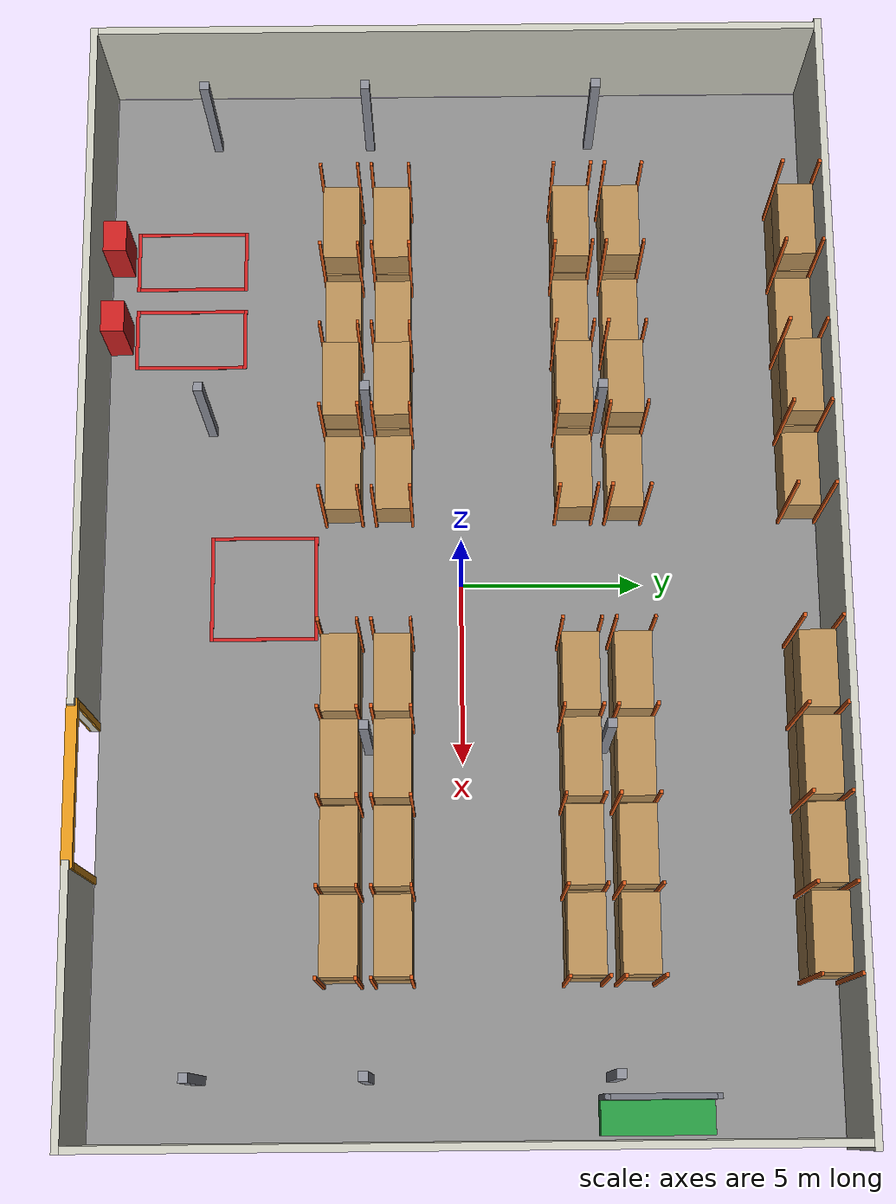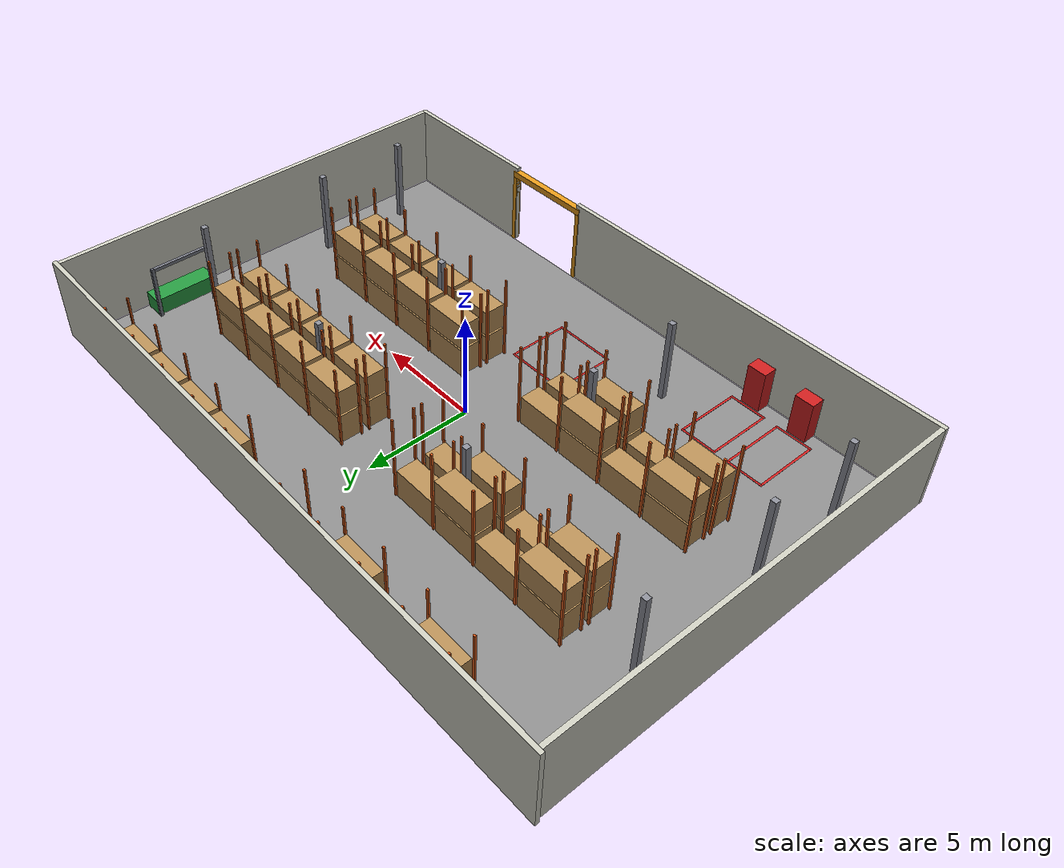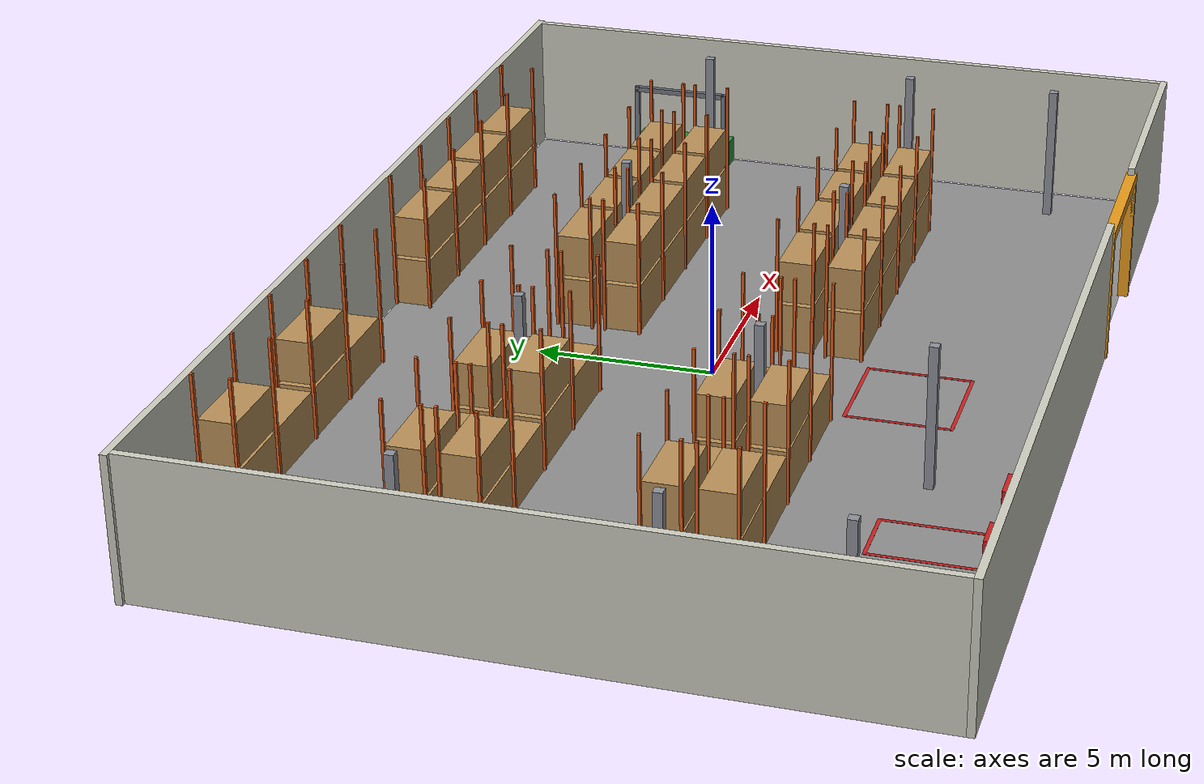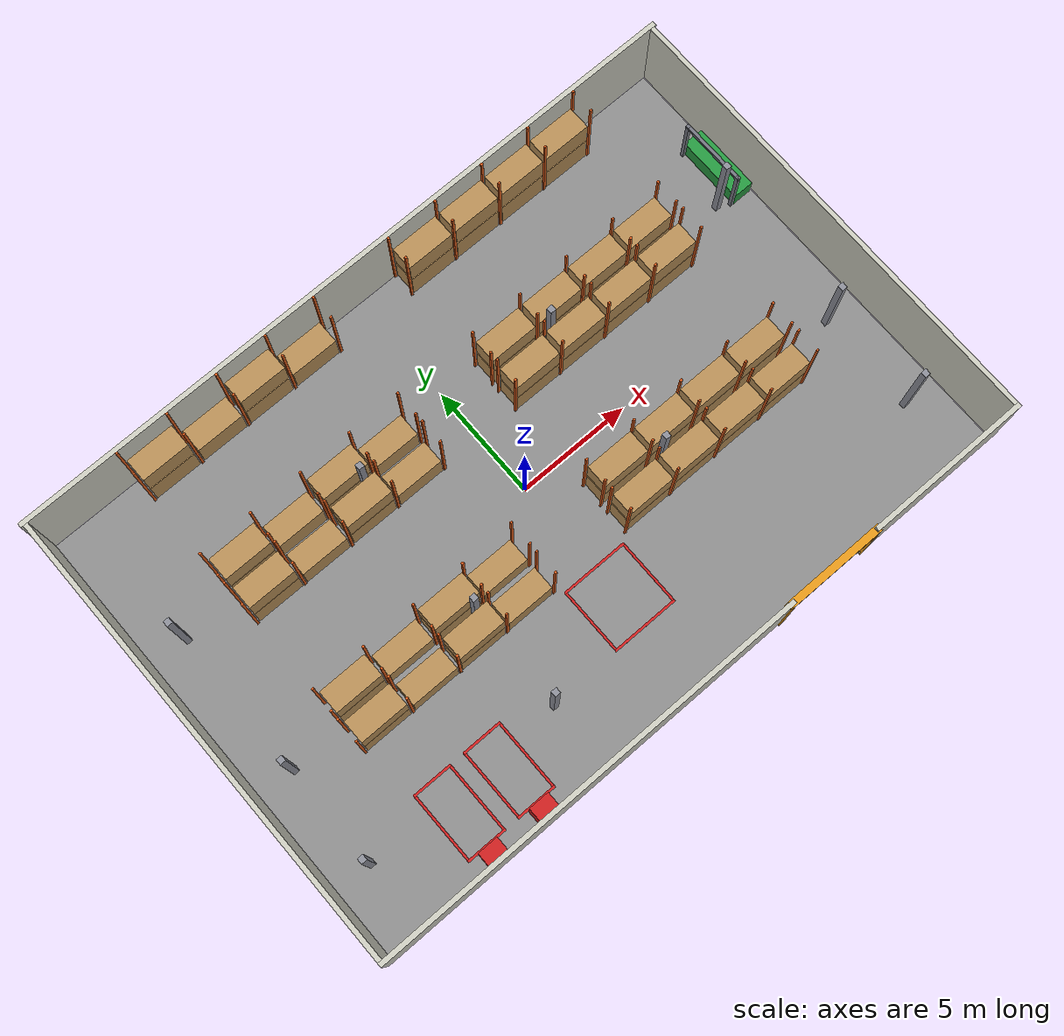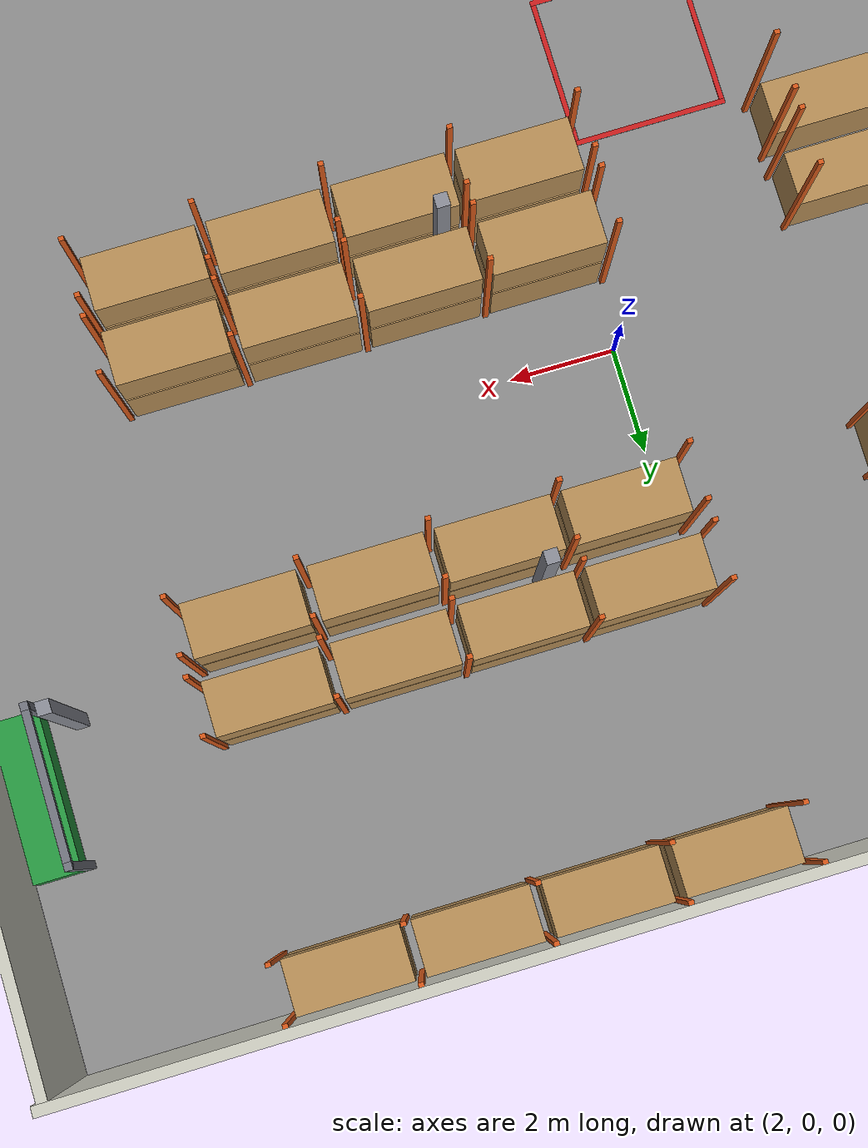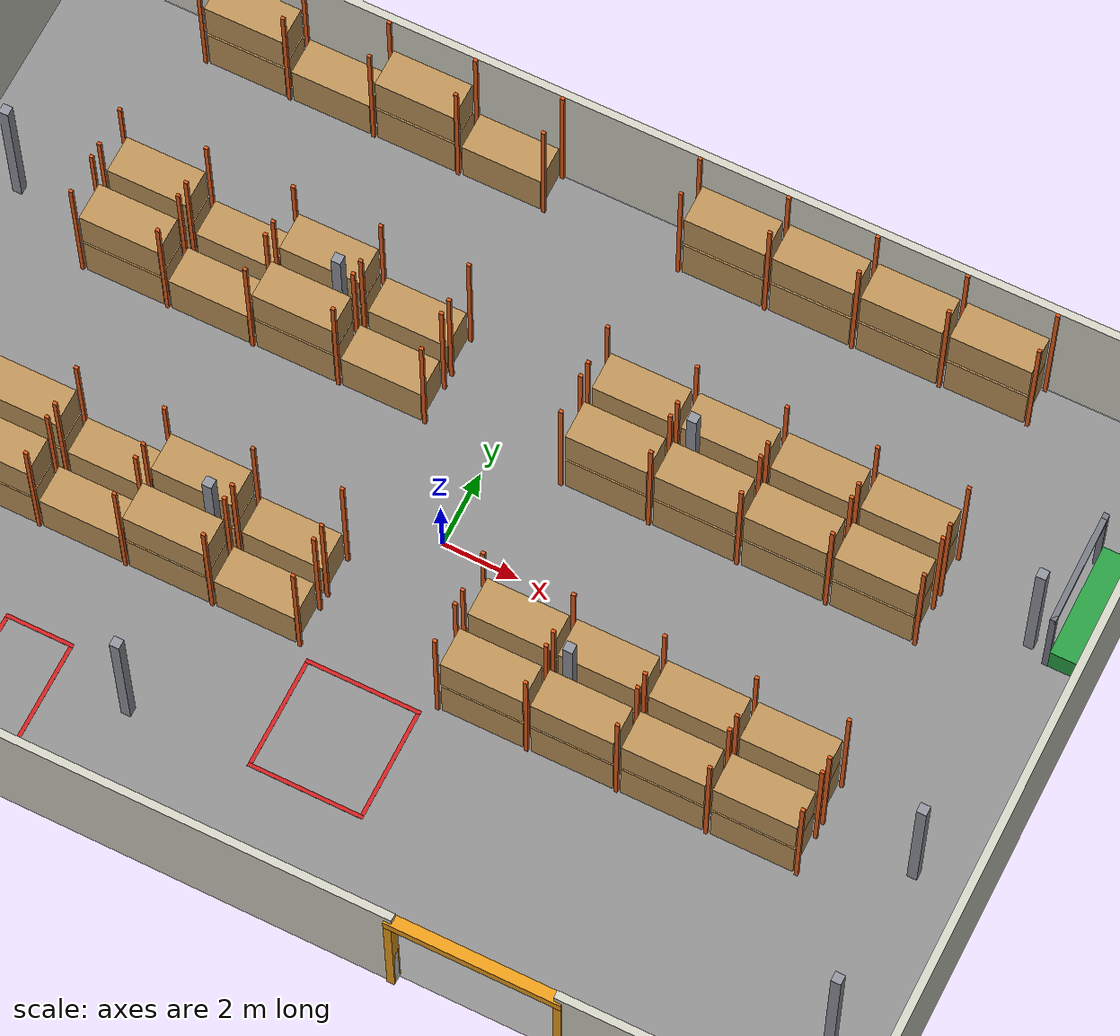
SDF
<?xml version="1.0" ?>
<sdf version="1.8">
  <world name="warehouse">

    <!-- The arena's 2 ms fixed step at 500 Hz, so joint rates measured on
         the M4 arena stay comparable here. -->
    <physics type="ode">
      <max_step_size>0.002</max_step_size>
      <real_time_factor>1.0</real_time_factor>
      <real_time_update_rate>500</real_time_update_rate>
    </physics>

    <plugin name="gz::sim::systems::Physics" filename="libgz-sim-physics-system.so"/>
    <plugin name="gz::sim::systems::UserCommands" filename="libgz-sim-user-commands-system.so"/>
    <plugin name="gz::sim::systems::SceneBroadcaster" filename="libgz-sim-scene-broadcaster-system.so"/>

    <!-- Required by the vehicle's three gpu_lidar sensors. Without this no
         scan topic is ever advertised and the failure is silent. -->
    <plugin name="gz::sim::systems::Sensors" filename="libgz-sim-sensors-system.so">
      <render_engine>ogre2</render_engine>
    </plugin>

    <!-- ======================= GUI CONFIGURATION ====================== -->
    <gui fullscreen="0">

      <plugin filename="MinimalScene" name="3D View">
        <gz-gui>
          <title>3D View</title>
          <property type="bool" key="showTitleBar">false</property>
          <property type="string" key="state">docked</property>
        </gz-gui>
        <engine>ogre2</engine>
        <scene>scene</scene>
        <ambient_light>1.0 1.0 1.0</ambient_light>
        <background_color>0.7 0.7 0.7</background_color>
        <!-- Looking north east from over the south west corner, so the
             dock apron, both charging bays and the west end of the rack
             block are in frame with no camera move. -->
        <camera_pose>-19.0 -16.0 12.0 0 0.52 0.72</camera_pose>
      </plugin>

      <plugin filename="GzSceneManager" name="Scene Manager">
        <gz-gui>
          <property key="resizable" type="bool">false</property>
          <property key="width" type="double">5</property>
          <property key="height" type="double">5</property>
          <property key="state" type="string">floating</property>
          <property key="showTitleBar" type="bool">false</property>
        </gz-gui>
      </plugin>

      <plugin filename="InteractiveViewControl" name="Interactive view control">
        <gz-gui>
          <property key="resizable" type="bool">false</property>
          <property key="width" type="double">5</property>
          <property key="height" type="double">5</property>
          <property key="state" type="string">floating</property>
          <property key="showTitleBar" type="bool">false</property>
        </gz-gui>
      </plugin>

      <plugin filename="CameraTracking" name="Camera Tracking">
        <gz-gui>
          <property key="resizable" type="bool">false</property>
          <property key="width" type="double">5</property>
          <property key="height" type="double">5</property>
          <property key="state" type="string">floating</property>
          <property key="showTitleBar" type="bool">false</property>
        </gz-gui>
      </plugin>

      <plugin filename="EntityContextMenuPlugin" name="Entity context menu">
        <gz-gui>
          <property key="state" type="string">floating</property>
          <property key="width" type="double">5</property>
          <property key="height" type="double">5</property>
          <property key="showTitleBar" type="bool">false</property>
        </gz-gui>
      </plugin>

      <plugin filename="WorldControl" name="World control">
        <gz-gui>
          <title>World control</title>
          <property type="bool" key="showTitleBar">false</property>
          <property type="bool" key="resizable">false</property>
          <property type="double" key="height">72</property>
          <property type="double" key="z">1</property>
          <property type="string" key="state">floating</property>
          <anchors target="3D View">
            <line own="left" target="left"/>
            <line own="bottom" target="bottom"/>
          </anchors>
        </gz-gui>
        <play_pause>true</play_pause>
        <step>true</step>
        <start_paused>false</start_paused>
        <use_event>true</use_event>
      </plugin>

      <!-- The real time factor readout, on screen for any recording. It is
           NOT a measurement instrument: the value it shows is gz's smoothed
           instantaneous factor. -->
      <plugin filename="WorldStats" name="World stats">
        <gz-gui>
          <title>World stats</title>
          <property type="bool" key="showTitleBar">false</property>
          <property type="bool" key="resizable">false</property>
          <property type="double" key="height">110</property>
          <property type="double" key="width">290</property>
          <property type="double" key="z">1</property>
          <property type="string" key="state">floating</property>
          <anchors target="3D View">
            <line own="right" target="right"/>
            <line own="bottom" target="bottom"/>
          </anchors>
        </gz-gui>
        <sim_time>true</sim_time>
        <real_time>true</real_time>
        <real_time_factor>true</real_time_factor>
        <iterations>true</iterations>
      </plugin>

      <!-- The beams. Docked rather than floating so the topic and display
           type combo boxes are visible without hunting: which scanner is on
           screen is not guessable from the picture. -->
      <plugin filename="VisualizeLidar" name="Visualize Lidar">
        <gz-gui>
          <title>Visualize lidar</title>
          <property type="string" key="state">docked</property>
        </gz-gui>
      </plugin>

      <plugin filename="Screenshot" name="Screenshot">
        <gz-gui>
          <property type="bool" key="showTitleBar">false</property>
          <property type="string" key="state">floating</property>
          <property type="double" key="width">100</property>
          <property type="double" key="height">50</property>
        </gz-gui>
      </plugin>

    </gui>

    <scene>
      <ambient>1 1 1 1</ambient>
      <background>0.7 0.7 0.7 1</background>
      <shadows>false</shadows>
      <grid>false</grid>
    </scene>

    <light name="sun" type="directional">
      <cast_shadows>false</cast_shadows>
      <pose>0 0 12 0 0 0</pose>
      <diffuse>1.0 1.0 1.0 1</diffuse>
      <specular>0.2 0.2 0.2 1</specular>
      <direction>-0.3 0.3 -1.0</direction>
    </light>

    <gravity>0 0 -9.8</gravity>

    <!-- ============================ Floor ============================ -->
    <!-- Plain concrete, mu 1.0 as in the arena: the tricycle has a single
         driven wheel and a slippery floor turns traction figures into tyre
         slip figures. -->
    <model name="Floor">
      <static>true</static>
      <link name="link">
        <collision name="collision">
          <geometry>
            <plane><normal>0 0 1</normal><size>30 20</size></plane>
          </geometry>
          <surface>
            <friction><ode><mu>1.0</mu><mu2>1.0</mu2></ode></friction>
          </surface>
        </collision>
        <visual name="visual">
          <geometry>
            <plane><normal>0 0 1</normal><size>30 20</size></plane>
          </geometry>
          <material>
            <ambient>0.55 0.55 0.55 1</ambient>
            <diffuse>0.55 0.55 0.55 1</diffuse>
          </material>
        </visual>
      </link>
    </model>

    <!-- ======================= Perimeter walls ======================= -->
    <!-- 0.20 thick, 4.00 high, inner faces at x = +-15.00 and
         y = +-10.00. The south wall is in two segments leaving the
         4.00 m dock door opening at x in [4.00, 8.00]. -->
    <model name="WallNorth">
      <static>true</static>
      <link name="link">
        <collision name="wallnorth_collision">
          <pose>0.000 10.100 2.000 0 0 0</pose>
          <geometry><box><size>30.600 0.200 4.000</size></box></geometry>
        </collision>
        <visual name="wallnorth_visual">
          <pose>0.000 10.100 2.000 0 0 0</pose>
          <geometry><box><size>30.600 0.200 4.000</size></box></geometry>
          <material><ambient>0.80 0.80 0.75 1</ambient><diffuse>0.80 0.80 0.75 1</diffuse></material>
        </visual>
      </link>
    </model>

    <model name="WallSouthWest">
      <static>true</static>
      <link name="link">
        <collision name="wallsouthwest_collision">
          <pose>-5.600 -10.100 2.000 0 0 0</pose>
          <geometry><box><size>19.200 0.200 4.000</size></box></geometry>
        </collision>
        <visual name="wallsouthwest_visual">
          <pose>-5.600 -10.100 2.000 0 0 0</pose>
          <geometry><box><size>19.200 0.200 4.000</size></box></geometry>
          <material><ambient>0.80 0.80 0.75 1</ambient><diffuse>0.80 0.80 0.75 1</diffuse></material>
        </visual>
      </link>
    </model>

    <model name="WallSouthEast">
      <static>true</static>
      <link name="link">
        <collision name="wallsoutheast_collision">
          <pose>11.600 -10.100 2.000 0 0 0</pose>
          <geometry><box><size>7.200 0.200 4.000</size></box></geometry>
        </collision>
        <visual name="wallsoutheast_visual">
          <pose>11.600 -10.100 2.000 0 0 0</pose>
          <geometry><box><size>7.200 0.200 4.000</size></box></geometry>
          <material><ambient>0.80 0.80 0.75 1</ambient><diffuse>0.80 0.80 0.75 1</diffuse></material>
        </visual>
      </link>
    </model>

    <model name="WallEast">
      <static>true</static>
      <link name="link">
        <collision name="walleast_collision">
          <pose>15.100 0.000 2.000 0 0 0</pose>
          <geometry><box><size>0.200 20.000 4.000</size></box></geometry>
        </collision>
        <visual name="walleast_visual">
          <pose>15.100 0.000 2.000 0 0 0</pose>
          <geometry><box><size>0.200 20.000 4.000</size></box></geometry>
          <material><ambient>0.80 0.80 0.75 1</ambient><diffuse>0.80 0.80 0.75 1</diffuse></material>
        </visual>
      </link>
    </model>

    <model name="WallWest">
      <static>true</static>
      <link name="link">
        <collision name="wallwest_collision">
          <pose>-15.100 0.000 2.000 0 0 0</pose>
          <geometry><box><size>0.200 20.000 4.000</size></box></geometry>
        </collision>
        <visual name="wallwest_visual">
          <pose>-15.100 0.000 2.000 0 0 0</pose>
          <geometry><box><size>0.200 20.000 4.000</size></box></geometry>
          <material><ambient>0.80 0.80 0.75 1</ambient><diffuse>0.80 0.80 0.75 1</diffuse></material>
        </visual>
      </link>
    </model>

    <!-- ========================= Dock door frame ====================== -->
    <model name="DoorGap">
      <static>true</static>
      <pose>6.00 -10.10 0 0 0 0</pose>
      <link name="link">
        <collision name="post_west_collision">
          <pose>-2.100 0.000 1.750 0 0 0</pose>
          <geometry><box><size>0.200 0.300 3.500</size></box></geometry>
        </collision>
        <visual name="post_west_visual">
          <pose>-2.100 0.000 1.750 0 0 0</pose>
          <geometry><box><size>0.200 0.300 3.500</size></box></geometry>
          <material><ambient>0.90 0.60 0.10 1</ambient><diffuse>0.90 0.60 0.10 1</diffuse></material>
        </visual>
        <collision name="post_east_collision">
          <pose>2.100 0.000 1.750 0 0 0</pose>
          <geometry><box><size>0.200 0.300 3.500</size></box></geometry>
        </collision>
        <visual name="post_east_visual">
          <pose>2.100 0.000 1.750 0 0 0</pose>
          <geometry><box><size>0.200 0.300 3.500</size></box></geometry>
          <material><ambient>0.90 0.60 0.10 1</ambient><diffuse>0.90 0.60 0.10 1</diffuse></material>
        </visual>
        <collision name="lintel_collision">
          <pose>0.000 0.000 3.650 0 0 0</pose>
          <geometry><box><size>4.400 0.300 0.300</size></box></geometry>
        </collision>
        <visual name="lintel_visual">
          <pose>0.000 0.000 3.650 0 0 0</pose>
          <geometry><box><size>4.400 0.300 0.300</size></box></geometry>
          <material><ambient>0.90 0.60 0.10 1</ambient><diffuse>0.90 0.60 0.10 1</diffuse></material>
        </visual>
      </link>
    </model>

    <!-- ============================ Racking =========================== -->

    <model name="RackRowA_West">
      <static>true</static>
      <link name="link">
        <!-- sub row A, front face y = +8.90, rear face y = +10.00 -->
        <collision name="a_frame0_front_collision">
          <pose>-11.000 8.940 2.000 0 0 0</pose>
          <geometry><box><size>0.100 0.080 4.000</size></box></geometry>
        </collision>
        <visual name="a_frame0_front_visual">
          <pose>-11.000 8.940 2.000 0 0 0</pose>
          <geometry><box><size>0.100 0.080 4.000</size></box></geometry>
          <material><ambient>0.85 0.35 0.10 1</ambient><diffuse>0.85 0.35 0.10 1</diffuse></material>
        </visual>
        <collision name="a_frame0_rear_collision">
          <pose>-11.000 9.960 2.000 0 0 0</pose>
          <geometry><box><size>0.100 0.080 4.000</size></box></geometry>
        </collision>
        <visual name="a_frame0_rear_visual">
          <pose>-11.000 9.960 2.000 0 0 0</pose>
          <geometry><box><size>0.100 0.080 4.000</size></box></geometry>
          <material><ambient>0.85 0.35 0.10 1</ambient><diffuse>0.85 0.35 0.10 1</diffuse></material>
        </visual>
        <collision name="a_frame1_front_collision">
          <pose>-8.700 8.940 2.000 0 0 0</pose>
          <geometry><box><size>0.100 0.080 4.000</size></box></geometry>
        </collision>
        <visual name="a_frame1_front_visual">
          <pose>-8.700 8.940 2.000 0 0 0</pose>
          <geometry><box><size>0.100 0.080 4.000</size></box></geometry>
          <material><ambient>0.85 0.35 0.10 1</ambient><diffuse>0.85 0.35 0.10 1</diffuse></material>
        </visual>
        <collision name="a_frame1_rear_collision">
          <pose>-8.700 9.960 2.000 0 0 0</pose>
          <geometry><box><size>0.100 0.080 4.000</size></box></geometry>
        </collision>
        <visual name="a_frame1_rear_visual">
          <pose>-8.700 9.960 2.000 0 0 0</pose>
          <geometry><box><size>0.100 0.080 4.000</size></box></geometry>
          <material><ambient>0.85 0.35 0.10 1</ambient><diffuse>0.85 0.35 0.10 1</diffuse></material>
        </visual>
        <collision name="a_frame2_front_collision">
          <pose>-6.400 8.940 2.000 0 0 0</pose>
          <geometry><box><size>0.100 0.080 4.000</size></box></geometry>
        </collision>
        <visual name="a_frame2_front_visual">
          <pose>-6.400 8.940 2.000 0 0 0</pose>
          <geometry><box><size>0.100 0.080 4.000</size></box></geometry>
          <material><ambient>0.85 0.35 0.10 1</ambient><diffuse>0.85 0.35 0.10 1</diffuse></material>
        </visual>
        <collision name="a_frame2_rear_collision">
          <pose>-6.400 9.960 2.000 0 0 0</pose>
          <geometry><box><size>0.100 0.080 4.000</size></box></geometry>
        </collision>
        <visual name="a_frame2_rear_visual">
          <pose>-6.400 9.960 2.000 0 0 0</pose>
          <geometry><box><size>0.100 0.080 4.000</size></box></geometry>
          <material><ambient>0.85 0.35 0.10 1</ambient><diffuse>0.85 0.35 0.10 1</diffuse></material>
        </visual>
        <collision name="a_frame3_front_collision">
          <pose>-4.100 8.940 2.000 0 0 0</pose>
          <geometry><box><size>0.100 0.080 4.000</size></box></geometry>
        </collision>
        <visual name="a_frame3_front_visual">
          <pose>-4.100 8.940 2.000 0 0 0</pose>
          <geometry><box><size>0.100 0.080 4.000</size></box></geometry>
          <material><ambient>0.85 0.35 0.10 1</ambient><diffuse>0.85 0.35 0.10 1</diffuse></material>
        </visual>
        <collision name="a_frame3_rear_collision">
          <pose>-4.100 9.960 2.000 0 0 0</pose>
          <geometry><box><size>0.100 0.080 4.000</size></box></geometry>
        </collision>
        <visual name="a_frame3_rear_visual">
          <pose>-4.100 9.960 2.000 0 0 0</pose>
          <geometry><box><size>0.100 0.080 4.000</size></box></geometry>
          <material><ambient>0.85 0.35 0.10 1</ambient><diffuse>0.85 0.35 0.10 1</diffuse></material>
        </visual>
        <collision name="a_frame4_front_collision">
          <pose>-1.800 8.940 2.000 0 0 0</pose>
          <geometry><box><size>0.100 0.080 4.000</size></box></geometry>
        </collision>
        <visual name="a_frame4_front_visual">
          <pose>-1.800 8.940 2.000 0 0 0</pose>
          <geometry><box><size>0.100 0.080 4.000</size></box></geometry>
          <material><ambient>0.85 0.35 0.10 1</ambient><diffuse>0.85 0.35 0.10 1</diffuse></material>
        </visual>
        <collision name="a_frame4_rear_collision">
          <pose>-1.800 9.960 2.000 0 0 0</pose>
          <geometry><box><size>0.100 0.080 4.000</size></box></geometry>
        </collision>
        <visual name="a_frame4_rear_visual">
          <pose>-1.800 9.960 2.000 0 0 0</pose>
          <geometry><box><size>0.100 0.080 4.000</size></box></geometry>
          <material><ambient>0.85 0.35 0.10 1</ambient><diffuse>0.85 0.35 0.10 1</diffuse></material>
        </visual>
        <collision name="a_bay0_level1_collision">
          <pose>-9.850 9.450 0.700 0 0 0</pose>
          <geometry><box><size>2.100 1.000 1.400</size></box></geometry>
        </collision>
        <visual name="a_bay0_level1_visual">
          <pose>-9.850 9.450 0.700 0 0 0</pose>
          <geometry><box><size>2.100 1.000 1.400</size></box></geometry>
          <material><ambient>0.72 0.56 0.34 1</ambient><diffuse>0.72 0.56 0.34 1</diffuse></material>
        </visual>
        <collision name="a_bay0_level2_collision">
          <pose>-9.850 9.450 2.100 0 0 0</pose>
          <geometry><box><size>2.100 1.000 1.200</size></box></geometry>
        </collision>
        <visual name="a_bay0_level2_visual">
          <pose>-9.850 9.450 2.100 0 0 0</pose>
          <geometry><box><size>2.100 1.000 1.200</size></box></geometry>
          <material><ambient>0.72 0.56 0.34 1</ambient><diffuse>0.72 0.56 0.34 1</diffuse></material>
        </visual>
        <collision name="a_bay1_level1_collision">
          <pose>-7.550 9.450 0.700 0 0 0</pose>
          <geometry><box><size>2.100 1.000 1.400</size></box></geometry>
        </collision>
        <visual name="a_bay1_level1_visual">
          <pose>-7.550 9.450 0.700 0 0 0</pose>
          <geometry><box><size>2.100 1.000 1.400</size></box></geometry>
          <material><ambient>0.72 0.56 0.34 1</ambient><diffuse>0.72 0.56 0.34 1</diffuse></material>
        </visual>
        <collision name="a_bay2_level1_collision">
          <pose>-5.250 9.450 0.700 0 0 0</pose>
          <geometry><box><size>2.100 1.000 1.400</size></box></geometry>
        </collision>
        <visual name="a_bay2_level1_visual">
          <pose>-5.250 9.450 0.700 0 0 0</pose>
          <geometry><box><size>2.100 1.000 1.400</size></box></geometry>
          <material><ambient>0.72 0.56 0.34 1</ambient><diffuse>0.72 0.56 0.34 1</diffuse></material>
        </visual>
        <collision name="a_bay2_level2_collision">
          <pose>-5.250 9.450 2.100 0 0 0</pose>
          <geometry><box><size>2.100 1.000 1.200</size></box></geometry>
        </collision>
        <visual name="a_bay2_level2_visual">
          <pose>-5.250 9.450 2.100 0 0 0</pose>
          <geometry><box><size>2.100 1.000 1.200</size></box></geometry>
          <material><ambient>0.72 0.56 0.34 1</ambient><diffuse>0.72 0.56 0.34 1</diffuse></material>
        </visual>
        <collision name="a_bay3_level1_collision">
          <pose>-2.950 9.450 0.700 0 0 0</pose>
          <geometry><box><size>2.100 1.000 1.400</size></box></geometry>
        </collision>
        <visual name="a_bay3_level1_visual">
          <pose>-2.950 9.450 0.700 0 0 0</pose>
          <geometry><box><size>2.100 1.000 1.400</size></box></geometry>
          <material><ambient>0.72 0.56 0.34 1</ambient><diffuse>0.72 0.56 0.34 1</diffuse></material>
        </visual>
      </link>
    </model>

    <model name="RackRowA_East">
      <static>true</static>
      <link name="link">
        <!-- sub row A, front face y = +8.90, rear face y = +10.00 -->
        <collision name="a_frame0_front_collision">
          <pose>1.800 8.940 2.000 0 0 0</pose>
          <geometry><box><size>0.100 0.080 4.000</size></box></geometry>
        </collision>
        <visual name="a_frame0_front_visual">
          <pose>1.800 8.940 2.000 0 0 0</pose>
          <geometry><box><size>0.100 0.080 4.000</size></box></geometry>
          <material><ambient>0.85 0.35 0.10 1</ambient><diffuse>0.85 0.35 0.10 1</diffuse></material>
        </visual>
        <collision name="a_frame0_rear_collision">
          <pose>1.800 9.960 2.000 0 0 0</pose>
          <geometry><box><size>0.100 0.080 4.000</size></box></geometry>
        </collision>
        <visual name="a_frame0_rear_visual">
          <pose>1.800 9.960 2.000 0 0 0</pose>
          <geometry><box><size>0.100 0.080 4.000</size></box></geometry>
          <material><ambient>0.85 0.35 0.10 1</ambient><diffuse>0.85 0.35 0.10 1</diffuse></material>
        </visual>
        <collision name="a_frame1_front_collision">
          <pose>4.100 8.940 2.000 0 0 0</pose>
          <geometry><box><size>0.100 0.080 4.000</size></box></geometry>
        </collision>
        <visual name="a_frame1_front_visual">
          <pose>4.100 8.940 2.000 0 0 0</pose>
          <geometry><box><size>0.100 0.080 4.000</size></box></geometry>
          <material><ambient>0.85 0.35 0.10 1</ambient><diffuse>0.85 0.35 0.10 1</diffuse></material>
        </visual>
        <collision name="a_frame1_rear_collision">
          <pose>4.100 9.960 2.000 0 0 0</pose>
          <geometry><box><size>0.100 0.080 4.000</size></box></geometry>
        </collision>
        <visual name="a_frame1_rear_visual">
          <pose>4.100 9.960 2.000 0 0 0</pose>
          <geometry><box><size>0.100 0.080 4.000</size></box></geometry>
          <material><ambient>0.85 0.35 0.10 1</ambient><diffuse>0.85 0.35 0.10 1</diffuse></material>
        </visual>
        <collision name="a_frame2_front_collision">
          <pose>6.400 8.940 2.000 0 0 0</pose>
          <geometry><box><size>0.100 0.080 4.000</size></box></geometry>
        </collision>
        <visual name="a_frame2_front_visual">
          <pose>6.400 8.940 2.000 0 0 0</pose>
          <geometry><box><size>0.100 0.080 4.000</size></box></geometry>
          <material><ambient>0.85 0.35 0.10 1</ambient><diffuse>0.85 0.35 0.10 1</diffuse></material>
        </visual>
        <collision name="a_frame2_rear_collision">
          <pose>6.400 9.960 2.000 0 0 0</pose>
          <geometry><box><size>0.100 0.080 4.000</size></box></geometry>
        </collision>
        <visual name="a_frame2_rear_visual">
          <pose>6.400 9.960 2.000 0 0 0</pose>
          <geometry><box><size>0.100 0.080 4.000</size></box></geometry>
          <material><ambient>0.85 0.35 0.10 1</ambient><diffuse>0.85 0.35 0.10 1</diffuse></material>
        </visual>
        <collision name="a_frame3_front_collision">
          <pose>8.700 8.940 2.000 0 0 0</pose>
          <geometry><box><size>0.100 0.080 4.000</size></box></geometry>
        </collision>
        <visual name="a_frame3_front_visual">
          <pose>8.700 8.940 2.000 0 0 0</pose>
          <geometry><box><size>0.100 0.080 4.000</size></box></geometry>
          <material><ambient>0.85 0.35 0.10 1</ambient><diffuse>0.85 0.35 0.10 1</diffuse></material>
        </visual>
        <collision name="a_frame3_rear_collision">
          <pose>8.700 9.960 2.000 0 0 0</pose>
          <geometry><box><size>0.100 0.080 4.000</size></box></geometry>
        </collision>
        <visual name="a_frame3_rear_visual">
          <pose>8.700 9.960 2.000 0 0 0</pose>
          <geometry><box><size>0.100 0.080 4.000</size></box></geometry>
          <material><ambient>0.85 0.35 0.10 1</ambient><diffuse>0.85 0.35 0.10 1</diffuse></material>
        </visual>
        <collision name="a_frame4_front_collision">
          <pose>11.000 8.940 2.000 0 0 0</pose>
          <geometry><box><size>0.100 0.080 4.000</size></box></geometry>
        </collision>
        <visual name="a_frame4_front_visual">
          <pose>11.000 8.940 2.000 0 0 0</pose>
          <geometry><box><size>0.100 0.080 4.000</size></box></geometry>
          <material><ambient>0.85 0.35 0.10 1</ambient><diffuse>0.85 0.35 0.10 1</diffuse></material>
        </visual>
        <collision name="a_frame4_rear_collision">
          <pose>11.000 9.960 2.000 0 0 0</pose>
          <geometry><box><size>0.100 0.080 4.000</size></box></geometry>
        </collision>
        <visual name="a_frame4_rear_visual">
          <pose>11.000 9.960 2.000 0 0 0</pose>
          <geometry><box><size>0.100 0.080 4.000</size></box></geometry>
          <material><ambient>0.85 0.35 0.10 1</ambient><diffuse>0.85 0.35 0.10 1</diffuse></material>
        </visual>
        <collision name="a_bay0_level1_collision">
          <pose>2.950 9.450 0.700 0 0 0</pose>
          <geometry><box><size>2.100 1.000 1.400</size></box></geometry>
        </collision>
        <visual name="a_bay0_level1_visual">
          <pose>2.950 9.450 0.700 0 0 0</pose>
          <geometry><box><size>2.100 1.000 1.400</size></box></geometry>
          <material><ambient>0.72 0.56 0.34 1</ambient><diffuse>0.72 0.56 0.34 1</diffuse></material>
        </visual>
        <collision name="a_bay0_level2_collision">
          <pose>2.950 9.450 2.100 0 0 0</pose>
          <geometry><box><size>2.100 1.000 1.200</size></box></geometry>
        </collision>
        <visual name="a_bay0_level2_visual">
          <pose>2.950 9.450 2.100 0 0 0</pose>
          <geometry><box><size>2.100 1.000 1.200</size></box></geometry>
          <material><ambient>0.72 0.56 0.34 1</ambient><diffuse>0.72 0.56 0.34 1</diffuse></material>
        </visual>
        <collision name="a_bay1_level1_collision">
          <pose>5.250 9.450 0.700 0 0 0</pose>
          <geometry><box><size>2.100 1.000 1.400</size></box></geometry>
        </collision>
        <visual name="a_bay1_level1_visual">
          <pose>5.250 9.450 0.700 0 0 0</pose>
          <geometry><box><size>2.100 1.000 1.400</size></box></geometry>
          <material><ambient>0.72 0.56 0.34 1</ambient><diffuse>0.72 0.56 0.34 1</diffuse></material>
        </visual>
        <collision name="a_bay1_level2_collision">
          <pose>5.250 9.450 2.100 0 0 0</pose>
          <geometry><box><size>2.100 1.000 1.200</size></box></geometry>
        </collision>
        <visual name="a_bay1_level2_visual">
          <pose>5.250 9.450 2.100 0 0 0</pose>
          <geometry><box><size>2.100 1.000 1.200</size></box></geometry>
          <material><ambient>0.72 0.56 0.34 1</ambient><diffuse>0.72 0.56 0.34 1</diffuse></material>
        </visual>
        <collision name="a_bay2_level1_collision">
          <pose>7.550 9.450 0.700 0 0 0</pose>
          <geometry><box><size>2.100 1.000 1.400</size></box></geometry>
        </collision>
        <visual name="a_bay2_level1_visual">
          <pose>7.550 9.450 0.700 0 0 0</pose>
          <geometry><box><size>2.100 1.000 1.400</size></box></geometry>
          <material><ambient>0.72 0.56 0.34 1</ambient><diffuse>0.72 0.56 0.34 1</diffuse></material>
        </visual>
        <collision name="a_bay2_level2_collision">
          <pose>7.550 9.450 2.100 0 0 0</pose>
          <geometry><box><size>2.100 1.000 1.200</size></box></geometry>
        </collision>
        <visual name="a_bay2_level2_visual">
          <pose>7.550 9.450 2.100 0 0 0</pose>
          <geometry><box><size>2.100 1.000 1.200</size></box></geometry>
          <material><ambient>0.72 0.56 0.34 1</ambient><diffuse>0.72 0.56 0.34 1</diffuse></material>
        </visual>
        <collision name="a_bay3_level1_collision">
          <pose>9.850 9.450 0.700 0 0 0</pose>
          <geometry><box><size>2.100 1.000 1.400</size></box></geometry>
        </collision>
        <visual name="a_bay3_level1_visual">
          <pose>9.850 9.450 0.700 0 0 0</pose>
          <geometry><box><size>2.100 1.000 1.400</size></box></geometry>
          <material><ambient>0.72 0.56 0.34 1</ambient><diffuse>0.72 0.56 0.34 1</diffuse></material>
        </visual>
        <collision name="a_bay3_level2_collision">
          <pose>9.850 9.450 2.100 0 0 0</pose>
          <geometry><box><size>2.100 1.000 1.200</size></box></geometry>
        </collision>
        <visual name="a_bay3_level2_visual">
          <pose>9.850 9.450 2.100 0 0 0</pose>
          <geometry><box><size>2.100 1.000 1.200</size></box></geometry>
          <material><ambient>0.72 0.56 0.34 1</ambient><diffuse>0.72 0.56 0.34 1</diffuse></material>
        </visual>
      </link>
    </model>

    <model name="RackRowB_West">
      <static>true</static>
      <link name="link">
        <!-- sub row Bn, front face y = +5.10, rear face y = +4.00 -->
        <collision name="bn_frame0_front_collision">
          <pose>-11.000 5.060 2.000 0 0 0</pose>
          <geometry><box><size>0.100 0.080 4.000</size></box></geometry>
        </collision>
        <visual name="bn_frame0_front_visual">
          <pose>-11.000 5.060 2.000 0 0 0</pose>
          <geometry><box><size>0.100 0.080 4.000</size></box></geometry>
          <material><ambient>0.85 0.35 0.10 1</ambient><diffuse>0.85 0.35 0.10 1</diffuse></material>
        </visual>
        <collision name="bn_frame0_rear_collision">
          <pose>-11.000 4.040 2.000 0 0 0</pose>
          <geometry><box><size>0.100 0.080 4.000</size></box></geometry>
        </collision>
        <visual name="bn_frame0_rear_visual">
          <pose>-11.000 4.040 2.000 0 0 0</pose>
          <geometry><box><size>0.100 0.080 4.000</size></box></geometry>
          <material><ambient>0.85 0.35 0.10 1</ambient><diffuse>0.85 0.35 0.10 1</diffuse></material>
        </visual>
        <collision name="bn_frame1_front_collision">
          <pose>-8.700 5.060 2.000 0 0 0</pose>
          <geometry><box><size>0.100 0.080 4.000</size></box></geometry>
        </collision>
        <visual name="bn_frame1_front_visual">
          <pose>-8.700 5.060 2.000 0 0 0</pose>
          <geometry><box><size>0.100 0.080 4.000</size></box></geometry>
          <material><ambient>0.85 0.35 0.10 1</ambient><diffuse>0.85 0.35 0.10 1</diffuse></material>
        </visual>
        <collision name="bn_frame1_rear_collision">
          <pose>-8.700 4.040 2.000 0 0 0</pose>
          <geometry><box><size>0.100 0.080 4.000</size></box></geometry>
        </collision>
        <visual name="bn_frame1_rear_visual">
          <pose>-8.700 4.040 2.000 0 0 0</pose>
          <geometry><box><size>0.100 0.080 4.000</size></box></geometry>
          <material><ambient>0.85 0.35 0.10 1</ambient><diffuse>0.85 0.35 0.10 1</diffuse></material>
        </visual>
        <collision name="bn_frame2_front_collision">
          <pose>-6.400 5.060 2.000 0 0 0</pose>
          <geometry><box><size>0.100 0.080 4.000</size></box></geometry>
        </collision>
        <visual name="bn_frame2_front_visual">
          <pose>-6.400 5.060 2.000 0 0 0</pose>
          <geometry><box><size>0.100 0.080 4.000</size></box></geometry>
          <material><ambient>0.85 0.35 0.10 1</ambient><diffuse>0.85 0.35 0.10 1</diffuse></material>
        </visual>
        <collision name="bn_frame2_rear_collision">
          <pose>-6.400 4.040 2.000 0 0 0</pose>
          <geometry><box><size>0.100 0.080 4.000</size></box></geometry>
        </collision>
        <visual name="bn_frame2_rear_visual">
          <pose>-6.400 4.040 2.000 0 0 0</pose>
          <geometry><box><size>0.100 0.080 4.000</size></box></geometry>
          <material><ambient>0.85 0.35 0.10 1</ambient><diffuse>0.85 0.35 0.10 1</diffuse></material>
        </visual>
        <collision name="bn_frame3_front_collision">
          <pose>-4.100 5.060 2.000 0 0 0</pose>
          <geometry><box><size>0.100 0.080 4.000</size></box></geometry>
        </collision>
        <visual name="bn_frame3_front_visual">
          <pose>-4.100 5.060 2.000 0 0 0</pose>
          <geometry><box><size>0.100 0.080 4.000</size></box></geometry>
          <material><ambient>0.85 0.35 0.10 1</ambient><diffuse>0.85 0.35 0.10 1</diffuse></material>
        </visual>
        <collision name="bn_frame3_rear_collision">
          <pose>-4.100 4.040 2.000 0 0 0</pose>
          <geometry><box><size>0.100 0.080 4.000</size></box></geometry>
        </collision>
        <visual name="bn_frame3_rear_visual">
          <pose>-4.100 4.040 2.000 0 0 0</pose>
          <geometry><box><size>0.100 0.080 4.000</size></box></geometry>
          <material><ambient>0.85 0.35 0.10 1</ambient><diffuse>0.85 0.35 0.10 1</diffuse></material>
        </visual>
        <collision name="bn_frame4_front_collision">
          <pose>-1.800 5.060 2.000 0 0 0</pose>
          <geometry><box><size>0.100 0.080 4.000</size></box></geometry>
        </collision>
        <visual name="bn_frame4_front_visual">
          <pose>-1.800 5.060 2.000 0 0 0</pose>
          <geometry><box><size>0.100 0.080 4.000</size></box></geometry>
          <material><ambient>0.85 0.35 0.10 1</ambient><diffuse>0.85 0.35 0.10 1</diffuse></material>
        </visual>
        <collision name="bn_frame4_rear_collision">
          <pose>-1.800 4.040 2.000 0 0 0</pose>
          <geometry><box><size>0.100 0.080 4.000</size></box></geometry>
        </collision>
        <visual name="bn_frame4_rear_visual">
          <pose>-1.800 4.040 2.000 0 0 0</pose>
          <geometry><box><size>0.100 0.080 4.000</size></box></geometry>
          <material><ambient>0.85 0.35 0.10 1</ambient><diffuse>0.85 0.35 0.10 1</diffuse></material>
        </visual>
        <collision name="bn_bay0_level1_collision">
          <pose>-9.850 4.550 0.700 0 0 0</pose>
          <geometry><box><size>2.100 1.000 1.400</size></box></geometry>
        </collision>
        <visual name="bn_bay0_level1_visual">
          <pose>-9.850 4.550 0.700 0 0 0</pose>
          <geometry><box><size>2.100 1.000 1.400</size></box></geometry>
          <material><ambient>0.72 0.56 0.34 1</ambient><diffuse>0.72 0.56 0.34 1</diffuse></material>
        </visual>
        <collision name="bn_bay0_level2_collision">
          <pose>-9.850 4.550 2.100 0 0 0</pose>
          <geometry><box><size>2.100 1.000 1.200</size></box></geometry>
        </collision>
        <visual name="bn_bay0_level2_visual">
          <pose>-9.850 4.550 2.100 0 0 0</pose>
          <geometry><box><size>2.100 1.000 1.200</size></box></geometry>
          <material><ambient>0.72 0.56 0.34 1</ambient><diffuse>0.72 0.56 0.34 1</diffuse></material>
        </visual>
        <collision name="bn_bay1_level1_collision">
          <pose>-7.550 4.550 0.700 0 0 0</pose>
          <geometry><box><size>2.100 1.000 1.400</size></box></geometry>
        </collision>
        <visual name="bn_bay1_level1_visual">
          <pose>-7.550 4.550 0.700 0 0 0</pose>
          <geometry><box><size>2.100 1.000 1.400</size></box></geometry>
          <material><ambient>0.72 0.56 0.34 1</ambient><diffuse>0.72 0.56 0.34 1</diffuse></material>
        </visual>
        <collision name="bn_bay2_level1_collision">
          <pose>-5.250 4.550 0.700 0 0 0</pose>
          <geometry><box><size>2.100 1.000 1.400</size></box></geometry>
        </collision>
        <visual name="bn_bay2_level1_visual">
          <pose>-5.250 4.550 0.700 0 0 0</pose>
          <geometry><box><size>2.100 1.000 1.400</size></box></geometry>
          <material><ambient>0.72 0.56 0.34 1</ambient><diffuse>0.72 0.56 0.34 1</diffuse></material>
        </visual>
        <collision name="bn_bay2_level2_collision">
          <pose>-5.250 4.550 2.100 0 0 0</pose>
          <geometry><box><size>2.100 1.000 1.200</size></box></geometry>
        </collision>
        <visual name="bn_bay2_level2_visual">
          <pose>-5.250 4.550 2.100 0 0 0</pose>
          <geometry><box><size>2.100 1.000 1.200</size></box></geometry>
          <material><ambient>0.72 0.56 0.34 1</ambient><diffuse>0.72 0.56 0.34 1</diffuse></material>
        </visual>
        <collision name="bn_bay3_level1_collision">
          <pose>-2.950 4.550 0.700 0 0 0</pose>
          <geometry><box><size>2.100 1.000 1.400</size></box></geometry>
        </collision>
        <visual name="bn_bay3_level1_visual">
          <pose>-2.950 4.550 0.700 0 0 0</pose>
          <geometry><box><size>2.100 1.000 1.400</size></box></geometry>
          <material><ambient>0.72 0.56 0.34 1</ambient><diffuse>0.72 0.56 0.34 1</diffuse></material>
        </visual>
        <!-- sub row Bs, front face y = +2.60, rear face y = +3.70 -->
        <collision name="bs_frame0_front_collision">
          <pose>-11.000 2.640 2.000 0 0 0</pose>
          <geometry><box><size>0.100 0.080 4.000</size></box></geometry>
        </collision>
        <visual name="bs_frame0_front_visual">
          <pose>-11.000 2.640 2.000 0 0 0</pose>
          <geometry><box><size>0.100 0.080 4.000</size></box></geometry>
          <material><ambient>0.85 0.35 0.10 1</ambient><diffuse>0.85 0.35 0.10 1</diffuse></material>
        </visual>
        <collision name="bs_frame0_rear_collision">
          <pose>-11.000 3.660 2.000 0 0 0</pose>
          <geometry><box><size>0.100 0.080 4.000</size></box></geometry>
        </collision>
        <visual name="bs_frame0_rear_visual">
          <pose>-11.000 3.660 2.000 0 0 0</pose>
          <geometry><box><size>0.100 0.080 4.000</size></box></geometry>
          <material><ambient>0.85 0.35 0.10 1</ambient><diffuse>0.85 0.35 0.10 1</diffuse></material>
        </visual>
        <collision name="bs_frame1_front_collision">
          <pose>-8.700 2.640 2.000 0 0 0</pose>
          <geometry><box><size>0.100 0.080 4.000</size></box></geometry>
        </collision>
        <visual name="bs_frame1_front_visual">
          <pose>-8.700 2.640 2.000 0 0 0</pose>
          <geometry><box><size>0.100 0.080 4.000</size></box></geometry>
          <material><ambient>0.85 0.35 0.10 1</ambient><diffuse>0.85 0.35 0.10 1</diffuse></material>
        </visual>
        <collision name="bs_frame1_rear_collision">
          <pose>-8.700 3.660 2.000 0 0 0</pose>
          <geometry><box><size>0.100 0.080 4.000</size></box></geometry>
        </collision>
        <visual name="bs_frame1_rear_visual">
          <pose>-8.700 3.660 2.000 0 0 0</pose>
          <geometry><box><size>0.100 0.080 4.000</size></box></geometry>
          <material><ambient>0.85 0.35 0.10 1</ambient><diffuse>0.85 0.35 0.10 1</diffuse></material>
        </visual>
        <collision name="bs_frame2_front_collision">
          <pose>-6.400 2.640 2.000 0 0 0</pose>
          <geometry><box><size>0.100 0.080 4.000</size></box></geometry>
        </collision>
        <visual name="bs_frame2_front_visual">
          <pose>-6.400 2.640 2.000 0 0 0</pose>
          <geometry><box><size>0.100 0.080 4.000</size></box></geometry>
          <material><ambient>0.85 0.35 0.10 1</ambient><diffuse>0.85 0.35 0.10 1</diffuse></material>
        </visual>
        <collision name="bs_frame2_rear_collision">
          <pose>-6.400 3.660 2.000 0 0 0</pose>
          <geometry><box><size>0.100 0.080 4.000</size></box></geometry>
        </collision>
        <visual name="bs_frame2_rear_visual">
          <pose>-6.400 3.660 2.000 0 0 0</pose>
          <geometry><box><size>0.100 0.080 4.000</size></box></geometry>
          <material><ambient>0.85 0.35 0.10 1</ambient><diffuse>0.85 0.35 0.10 1</diffuse></material>
        </visual>
        <collision name="bs_frame3_front_collision">
          <pose>-4.100 2.640 2.000 0 0 0</pose>
          <geometry><box><size>0.100 0.080 4.000</size></box></geometry>
        </collision>
        <visual name="bs_frame3_front_visual">
          <pose>-4.100 2.640 2.000 0 0 0</pose>
          <geometry><box><size>0.100 0.080 4.000</size></box></geometry>
          <material><ambient>0.85 0.35 0.10 1</ambient><diffuse>0.85 0.35 0.10 1</diffuse></material>
        </visual>
        <collision name="bs_frame3_rear_collision">
          <pose>-4.100 3.660 2.000 0 0 0</pose>
          <geometry><box><size>0.100 0.080 4.000</size></box></geometry>
        </collision>
        <visual name="bs_frame3_rear_visual">
          <pose>-4.100 3.660 2.000 0 0 0</pose>
          <geometry><box><size>0.100 0.080 4.000</size></box></geometry>
          <material><ambient>0.85 0.35 0.10 1</ambient><diffuse>0.85 0.35 0.10 1</diffuse></material>
        </visual>
        <collision name="bs_frame4_front_collision">
          <pose>-1.800 2.640 2.000 0 0 0</pose>
          <geometry><box><size>0.100 0.080 4.000</size></box></geometry>
        </collision>
        <visual name="bs_frame4_front_visual">
          <pose>-1.800 2.640 2.000 0 0 0</pose>
          <geometry><box><size>0.100 0.080 4.000</size></box></geometry>
          <material><ambient>0.85 0.35 0.10 1</ambient><diffuse>0.85 0.35 0.10 1</diffuse></material>
        </visual>
        <collision name="bs_frame4_rear_collision">
          <pose>-1.800 3.660 2.000 0 0 0</pose>
          <geometry><box><size>0.100 0.080 4.000</size></box></geometry>
        </collision>
        <visual name="bs_frame4_rear_visual">
          <pose>-1.800 3.660 2.000 0 0 0</pose>
          <geometry><box><size>0.100 0.080 4.000</size></box></geometry>
          <material><ambient>0.85 0.35 0.10 1</ambient><diffuse>0.85 0.35 0.10 1</diffuse></material>
        </visual>
        <collision name="bs_bay0_level1_collision">
          <pose>-9.850 3.150 0.700 0 0 0</pose>
          <geometry><box><size>2.100 1.000 1.400</size></box></geometry>
        </collision>
        <visual name="bs_bay0_level1_visual">
          <pose>-9.850 3.150 0.700 0 0 0</pose>
          <geometry><box><size>2.100 1.000 1.400</size></box></geometry>
          <material><ambient>0.72 0.56 0.34 1</ambient><diffuse>0.72 0.56 0.34 1</diffuse></material>
        </visual>
        <collision name="bs_bay0_level2_collision">
          <pose>-9.850 3.150 2.100 0 0 0</pose>
          <geometry><box><size>2.100 1.000 1.200</size></box></geometry>
        </collision>
        <visual name="bs_bay0_level2_visual">
          <pose>-9.850 3.150 2.100 0 0 0</pose>
          <geometry><box><size>2.100 1.000 1.200</size></box></geometry>
          <material><ambient>0.72 0.56 0.34 1</ambient><diffuse>0.72 0.56 0.34 1</diffuse></material>
        </visual>
        <collision name="bs_bay1_level1_collision">
          <pose>-7.550 3.150 0.700 0 0 0</pose>
          <geometry><box><size>2.100 1.000 1.400</size></box></geometry>
        </collision>
        <visual name="bs_bay1_level1_visual">
          <pose>-7.550 3.150 0.700 0 0 0</pose>
          <geometry><box><size>2.100 1.000 1.400</size></box></geometry>
          <material><ambient>0.72 0.56 0.34 1</ambient><diffuse>0.72 0.56 0.34 1</diffuse></material>
        </visual>
        <collision name="bs_bay2_level1_collision">
          <pose>-5.250 3.150 0.700 0 0 0</pose>
          <geometry><box><size>2.100 1.000 1.400</size></box></geometry>
        </collision>
        <visual name="bs_bay2_level1_visual">
          <pose>-5.250 3.150 0.700 0 0 0</pose>
          <geometry><box><size>2.100 1.000 1.400</size></box></geometry>
          <material><ambient>0.72 0.56 0.34 1</ambient><diffuse>0.72 0.56 0.34 1</diffuse></material>
        </visual>
        <collision name="bs_bay2_level2_collision">
          <pose>-5.250 3.150 2.100 0 0 0</pose>
          <geometry><box><size>2.100 1.000 1.200</size></box></geometry>
        </collision>
        <visual name="bs_bay2_level2_visual">
          <pose>-5.250 3.150 2.100 0 0 0</pose>
          <geometry><box><size>2.100 1.000 1.200</size></box></geometry>
          <material><ambient>0.72 0.56 0.34 1</ambient><diffuse>0.72 0.56 0.34 1</diffuse></material>
        </visual>
        <collision name="bs_bay3_level1_collision">
          <pose>-2.950 3.150 0.700 0 0 0</pose>
          <geometry><box><size>2.100 1.000 1.400</size></box></geometry>
        </collision>
        <visual name="bs_bay3_level1_visual">
          <pose>-2.950 3.150 0.700 0 0 0</pose>
          <geometry><box><size>2.100 1.000 1.400</size></box></geometry>
          <material><ambient>0.72 0.56 0.34 1</ambient><diffuse>0.72 0.56 0.34 1</diffuse></material>
        </visual>
      </link>
    </model>

    <model name="RackRowB_East">
      <static>true</static>
      <link name="link">
        <!-- sub row Bn, front face y = +5.10, rear face y = +4.00 -->
        <collision name="bn_frame0_front_collision">
          <pose>1.800 5.060 2.000 0 0 0</pose>
          <geometry><box><size>0.100 0.080 4.000</size></box></geometry>
        </collision>
        <visual name="bn_frame0_front_visual">
          <pose>1.800 5.060 2.000 0 0 0</pose>
          <geometry><box><size>0.100 0.080 4.000</size></box></geometry>
          <material><ambient>0.85 0.35 0.10 1</ambient><diffuse>0.85 0.35 0.10 1</diffuse></material>
        </visual>
        <collision name="bn_frame0_rear_collision">
          <pose>1.800 4.040 2.000 0 0 0</pose>
          <geometry><box><size>0.100 0.080 4.000</size></box></geometry>
        </collision>
        <visual name="bn_frame0_rear_visual">
          <pose>1.800 4.040 2.000 0 0 0</pose>
          <geometry><box><size>0.100 0.080 4.000</size></box></geometry>
          <material><ambient>0.85 0.35 0.10 1</ambient><diffuse>0.85 0.35 0.10 1</diffuse></material>
        </visual>
        <collision name="bn_frame1_front_collision">
          <pose>4.100 5.060 2.000 0 0 0</pose>
          <geometry><box><size>0.100 0.080 4.000</size></box></geometry>
        </collision>
        <visual name="bn_frame1_front_visual">
          <pose>4.100 5.060 2.000 0 0 0</pose>
          <geometry><box><size>0.100 0.080 4.000</size></box></geometry>
          <material><ambient>0.85 0.35 0.10 1</ambient><diffuse>0.85 0.35 0.10 1</diffuse></material>
        </visual>
        <collision name="bn_frame1_rear_collision">
          <pose>4.100 4.040 2.000 0 0 0</pose>
          <geometry><box><size>0.100 0.080 4.000</size></box></geometry>
        </collision>
        <visual name="bn_frame1_rear_visual">
          <pose>4.100 4.040 2.000 0 0 0</pose>
          <geometry><box><size>0.100 0.080 4.000</size></box></geometry>
          <material><ambient>0.85 0.35 0.10 1</ambient><diffuse>0.85 0.35 0.10 1</diffuse></material>
        </visual>
        <collision name="bn_frame2_front_collision">
          <pose>6.400 5.060 2.000 0 0 0</pose>
          <geometry><box><size>0.100 0.080 4.000</size></box></geometry>
        </collision>
        <visual name="bn_frame2_front_visual">
          <pose>6.400 5.060 2.000 0 0 0</pose>
          <geometry><box><size>0.100 0.080 4.000</size></box></geometry>
          <material><ambient>0.85 0.35 0.10 1</ambient><diffuse>0.85 0.35 0.10 1</diffuse></material>
        </visual>
        <collision name="bn_frame2_rear_collision">
          <pose>6.400 4.040 2.000 0 0 0</pose>
          <geometry><box><size>0.100 0.080 4.000</size></box></geometry>
        </collision>
        <visual name="bn_frame2_rear_visual">
          <pose>6.400 4.040 2.000 0 0 0</pose>
          <geometry><box><size>0.100 0.080 4.000</size></box></geometry>
          <material><ambient>0.85 0.35 0.10 1</ambient><diffuse>0.85 0.35 0.10 1</diffuse></material>
        </visual>
        <collision name="bn_frame3_front_collision">
          <pose>8.700 5.060 2.000 0 0 0</pose>
          <geometry><box><size>0.100 0.080 4.000</size></box></geometry>
        </collision>
        <visual name="bn_frame3_front_visual">
          <pose>8.700 5.060 2.000 0 0 0</pose>
          <geometry><box><size>0.100 0.080 4.000</size></box></geometry>
          <material><ambient>0.85 0.35 0.10 1</ambient><diffuse>0.85 0.35 0.10 1</diffuse></material>
        </visual>
        <collision name="bn_frame3_rear_collision">
          <pose>8.700 4.040 2.000 0 0 0</pose>
          <geometry><box><size>0.100 0.080 4.000</size></box></geometry>
        </collision>
        <visual name="bn_frame3_rear_visual">
          <pose>8.700 4.040 2.000 0 0 0</pose>
          <geometry><box><size>0.100 0.080 4.000</size></box></geometry>
          <material><ambient>0.85 0.35 0.10 1</ambient><diffuse>0.85 0.35 0.10 1</diffuse></material>
        </visual>
        <collision name="bn_frame4_front_collision">
          <pose>11.000 5.060 2.000 0 0 0</pose>
          <geometry><box><size>0.100 0.080 4.000</size></box></geometry>
        </collision>
        <visual name="bn_frame4_front_visual">
          <pose>11.000 5.060 2.000 0 0 0</pose>
          <geometry><box><size>0.100 0.080 4.000</size></box></geometry>
          <material><ambient>0.85 0.35 0.10 1</ambient><diffuse>0.85 0.35 0.10 1</diffuse></material>
        </visual>
        <collision name="bn_frame4_rear_collision">
          <pose>11.000 4.040 2.000 0 0 0</pose>
          <geometry><box><size>0.100 0.080 4.000</size></box></geometry>
        </collision>
        <visual name="bn_frame4_rear_visual">
          <pose>11.000 4.040 2.000 0 0 0</pose>
          <geometry><box><size>0.100 0.080 4.000</size></box></geometry>
          <material><ambient>0.85 0.35 0.10 1</ambient><diffuse>0.85 0.35 0.10 1</diffuse></material>
        </visual>
        <collision name="bn_bay0_level1_collision">
          <pose>2.950 4.550 0.700 0 0 0</pose>
          <geometry><box><size>2.100 1.000 1.400</size></box></geometry>
        </collision>
        <visual name="bn_bay0_level1_visual">
          <pose>2.950 4.550 0.700 0 0 0</pose>
          <geometry><box><size>2.100 1.000 1.400</size></box></geometry>
          <material><ambient>0.72 0.56 0.34 1</ambient><diffuse>0.72 0.56 0.34 1</diffuse></material>
        </visual>
        <collision name="bn_bay0_level2_collision">
          <pose>2.950 4.550 2.100 0 0 0</pose>
          <geometry><box><size>2.100 1.000 1.200</size></box></geometry>
        </collision>
        <visual name="bn_bay0_level2_visual">
          <pose>2.950 4.550 2.100 0 0 0</pose>
          <geometry><box><size>2.100 1.000 1.200</size></box></geometry>
          <material><ambient>0.72 0.56 0.34 1</ambient><diffuse>0.72 0.56 0.34 1</diffuse></material>
        </visual>
        <collision name="bn_bay1_level1_collision">
          <pose>5.250 4.550 0.700 0 0 0</pose>
          <geometry><box><size>2.100 1.000 1.400</size></box></geometry>
        </collision>
        <visual name="bn_bay1_level1_visual">
          <pose>5.250 4.550 0.700 0 0 0</pose>
          <geometry><box><size>2.100 1.000 1.400</size></box></geometry>
          <material><ambient>0.72 0.56 0.34 1</ambient><diffuse>0.72 0.56 0.34 1</diffuse></material>
        </visual>
        <collision name="bn_bay1_level2_collision">
          <pose>5.250 4.550 2.100 0 0 0</pose>
          <geometry><box><size>2.100 1.000 1.200</size></box></geometry>
        </collision>
        <visual name="bn_bay1_level2_visual">
          <pose>5.250 4.550 2.100 0 0 0</pose>
          <geometry><box><size>2.100 1.000 1.200</size></box></geometry>
          <material><ambient>0.72 0.56 0.34 1</ambient><diffuse>0.72 0.56 0.34 1</diffuse></material>
        </visual>
        <collision name="bn_bay2_level1_collision">
          <pose>7.550 4.550 0.700 0 0 0</pose>
          <geometry><box><size>2.100 1.000 1.400</size></box></geometry>
        </collision>
        <visual name="bn_bay2_level1_visual">
          <pose>7.550 4.550 0.700 0 0 0</pose>
          <geometry><box><size>2.100 1.000 1.400</size></box></geometry>
          <material><ambient>0.72 0.56 0.34 1</ambient><diffuse>0.72 0.56 0.34 1</diffuse></material>
        </visual>
        <collision name="bn_bay2_level2_collision">
          <pose>7.550 4.550 2.100 0 0 0</pose>
          <geometry><box><size>2.100 1.000 1.200</size></box></geometry>
        </collision>
        <visual name="bn_bay2_level2_visual">
          <pose>7.550 4.550 2.100 0 0 0</pose>
          <geometry><box><size>2.100 1.000 1.200</size></box></geometry>
          <material><ambient>0.72 0.56 0.34 1</ambient><diffuse>0.72 0.56 0.34 1</diffuse></material>
        </visual>
        <collision name="bn_bay3_level1_collision">
          <pose>9.850 4.550 0.700 0 0 0</pose>
          <geometry><box><size>2.100 1.000 1.400</size></box></geometry>
        </collision>
        <visual name="bn_bay3_level1_visual">
          <pose>9.850 4.550 0.700 0 0 0</pose>
          <geometry><box><size>2.100 1.000 1.400</size></box></geometry>
          <material><ambient>0.72 0.56 0.34 1</ambient><diffuse>0.72 0.56 0.34 1</diffuse></material>
        </visual>
        <collision name="bn_bay3_level2_collision">
          <pose>9.850 4.550 2.100 0 0 0</pose>
          <geometry><box><size>2.100 1.000 1.200</size></box></geometry>
        </collision>
        <visual name="bn_bay3_level2_visual">
          <pose>9.850 4.550 2.100 0 0 0</pose>
          <geometry><box><size>2.100 1.000 1.200</size></box></geometry>
          <material><ambient>0.72 0.56 0.34 1</ambient><diffuse>0.72 0.56 0.34 1</diffuse></material>
        </visual>
        <!-- sub row Bs, front face y = +2.60, rear face y = +3.70 -->
        <collision name="bs_frame0_front_collision">
          <pose>1.800 2.640 2.000 0 0 0</pose>
          <geometry><box><size>0.100 0.080 4.000</size></box></geometry>
        </collision>
        <visual name="bs_frame0_front_visual">
          <pose>1.800 2.640 2.000 0 0 0</pose>
          <geometry><box><size>0.100 0.080 4.000</size></box></geometry>
          <material><ambient>0.85 0.35 0.10 1</ambient><diffuse>0.85 0.35 0.10 1</diffuse></material>
        </visual>
        <collision name="bs_frame0_rear_collision">
          <pose>1.800 3.660 2.000 0 0 0</pose>
          <geometry><box><size>0.100 0.080 4.000</size></box></geometry>
        </collision>
        <visual name="bs_frame0_rear_visual">
          <pose>1.800 3.660 2.000 0 0 0</pose>
          <geometry><box><size>0.100 0.080 4.000</size></box></geometry>
          <material><ambient>0.85 0.35 0.10 1</ambient><diffuse>0.85 0.35 0.10 1</diffuse></material>
        </visual>
        <collision name="bs_frame1_front_collision">
          <pose>4.100 2.640 2.000 0 0 0</pose>
          <geometry><box><size>0.100 0.080 4.000</size></box></geometry>
        </collision>
        <visual name="bs_frame1_front_visual">
          <pose>4.100 2.640 2.000 0 0 0</pose>
          <geometry><box><size>0.100 0.080 4.000</size></box></geometry>
          <material><ambient>0.85 0.35 0.10 1</ambient><diffuse>0.85 0.35 0.10 1</diffuse></material>
        </visual>
        <collision name="bs_frame1_rear_collision">
          <pose>4.100 3.660 2.000 0 0 0</pose>
          <geometry><box><size>0.100 0.080 4.000</size></box></geometry>
        </collision>
        <visual name="bs_frame1_rear_visual">
          <pose>4.100 3.660 2.000 0 0 0</pose>
          <geometry><box><size>0.100 0.080 4.000</size></box></geometry>
          <material><ambient>0.85 0.35 0.10 1</ambient><diffuse>0.85 0.35 0.10 1</diffuse></material>
        </visual>
        <collision name="bs_frame2_front_collision">
          <pose>6.400 2.640 2.000 0 0 0</pose>
          <geometry><box><size>0.100 0.080 4.000</size></box></geometry>
        </collision>
        <visual name="bs_frame2_front_visual">
          <pose>6.400 2.640 2.000 0 0 0</pose>
          <geometry><box><size>0.100 0.080 4.000</size></box></geometry>
          <material><ambient>0.85 0.35 0.10 1</ambient><diffuse>0.85 0.35 0.10 1</diffuse></material>
        </visual>
        <collision name="bs_frame2_rear_collision">
          <pose>6.400 3.660 2.000 0 0 0</pose>
          <geometry><box><size>0.100 0.080 4.000</size></box></geometry>
        </collision>
        <visual name="bs_frame2_rear_visual">
          <pose>6.400 3.660 2.000 0 0 0</pose>
          <geometry><box><size>0.100 0.080 4.000</size></box></geometry>
          <material><ambient>0.85 0.35 0.10 1</ambient><diffuse>0.85 0.35 0.10 1</diffuse></material>
        </visual>
        <collision name="bs_frame3_front_collision">
          <pose>8.700 2.640 2.000 0 0 0</pose>
          <geometry><box><size>0.100 0.080 4.000</size></box></geometry>
        </collision>
        <visual name="bs_frame3_front_visual">
          <pose>8.700 2.640 2.000 0 0 0</pose>
          <geometry><box><size>0.100 0.080 4.000</size></box></geometry>
          <material><ambient>0.85 0.35 0.10 1</ambient><diffuse>0.85 0.35 0.10 1</diffuse></material>
        </visual>
        <collision name="bs_frame3_rear_collision">
          <pose>8.700 3.660 2.000 0 0 0</pose>
          <geometry><box><size>0.100 0.080 4.000</size></box></geometry>
        </collision>
        <visual name="bs_frame3_rear_visual">
          <pose>8.700 3.660 2.000 0 0 0</pose>
          <geometry><box><size>0.100 0.080 4.000</size></box></geometry>
          <material><ambient>0.85 0.35 0.10 1</ambient><diffuse>0.85 0.35 0.10 1</diffuse></material>
        </visual>
        <collision name="bs_frame4_front_collision">
          <pose>11.000 2.640 2.000 0 0 0</pose>
          <geometry><box><size>0.100 0.080 4.000</size></box></geometry>
        </collision>
        <visual name="bs_frame4_front_visual">
          <pose>11.000 2.640 2.000 0 0 0</pose>
          <geometry><box><size>0.100 0.080 4.000</size></box></geometry>
          <material><ambient>0.85 0.35 0.10 1</ambient><diffuse>0.85 0.35 0.10 1</diffuse></material>
        </visual>
        <collision name="bs_frame4_rear_collision">
          <pose>11.000 3.660 2.000 0 0 0</pose>
          <geometry><box><size>0.100 0.080 4.000</size></box></geometry>
        </collision>
        <visual name="bs_frame4_rear_visual">
          <pose>11.000 3.660 2.000 0 0 0</pose>
          <geometry><box><size>0.100 0.080 4.000</size></box></geometry>
          <material><ambient>0.85 0.35 0.10 1</ambient><diffuse>0.85 0.35 0.10 1</diffuse></material>
        </visual>
        <collision name="bs_bay0_level1_collision">
          <pose>2.950 3.150 0.700 0 0 0</pose>
          <geometry><box><size>2.100 1.000 1.400</size></box></geometry>
        </collision>
        <visual name="bs_bay0_level1_visual">
          <pose>2.950 3.150 0.700 0 0 0</pose>
          <geometry><box><size>2.100 1.000 1.400</size></box></geometry>
          <material><ambient>0.72 0.56 0.34 1</ambient><diffuse>0.72 0.56 0.34 1</diffuse></material>
        </visual>
        <collision name="bs_bay0_level2_collision">
          <pose>2.950 3.150 2.100 0 0 0</pose>
          <geometry><box><size>2.100 1.000 1.200</size></box></geometry>
        </collision>
        <visual name="bs_bay0_level2_visual">
          <pose>2.950 3.150 2.100 0 0 0</pose>
          <geometry><box><size>2.100 1.000 1.200</size></box></geometry>
          <material><ambient>0.72 0.56 0.34 1</ambient><diffuse>0.72 0.56 0.34 1</diffuse></material>
        </visual>
        <collision name="bs_bay1_level1_collision">
          <pose>5.250 3.150 0.700 0 0 0</pose>
          <geometry><box><size>2.100 1.000 1.400</size></box></geometry>
        </collision>
        <visual name="bs_bay1_level1_visual">
          <pose>5.250 3.150 0.700 0 0 0</pose>
          <geometry><box><size>2.100 1.000 1.400</size></box></geometry>
          <material><ambient>0.72 0.56 0.34 1</ambient><diffuse>0.72 0.56 0.34 1</diffuse></material>
        </visual>
        <collision name="bs_bay1_level2_collision">
          <pose>5.250 3.150 2.100 0 0 0</pose>
          <geometry><box><size>2.100 1.000 1.200</size></box></geometry>
        </collision>
        <visual name="bs_bay1_level2_visual">
          <pose>5.250 3.150 2.100 0 0 0</pose>
          <geometry><box><size>2.100 1.000 1.200</size></box></geometry>
          <material><ambient>0.72 0.56 0.34 1</ambient><diffuse>0.72 0.56 0.34 1</diffuse></material>
        </visual>
        <collision name="bs_bay2_level1_collision">
          <pose>7.550 3.150 0.700 0 0 0</pose>
          <geometry><box><size>2.100 1.000 1.400</size></box></geometry>
        </collision>
        <visual name="bs_bay2_level1_visual">
          <pose>7.550 3.150 0.700 0 0 0</pose>
          <geometry><box><size>2.100 1.000 1.400</size></box></geometry>
          <material><ambient>0.72 0.56 0.34 1</ambient><diffuse>0.72 0.56 0.34 1</diffuse></material>
        </visual>
        <collision name="bs_bay2_level2_collision">
          <pose>7.550 3.150 2.100 0 0 0</pose>
          <geometry><box><size>2.100 1.000 1.200</size></box></geometry>
        </collision>
        <visual name="bs_bay2_level2_visual">
          <pose>7.550 3.150 2.100 0 0 0</pose>
          <geometry><box><size>2.100 1.000 1.200</size></box></geometry>
          <material><ambient>0.72 0.56 0.34 1</ambient><diffuse>0.72 0.56 0.34 1</diffuse></material>
        </visual>
        <collision name="bs_bay3_level1_collision">
          <pose>9.850 3.150 0.700 0 0 0</pose>
          <geometry><box><size>2.100 1.000 1.400</size></box></geometry>
        </collision>
        <visual name="bs_bay3_level1_visual">
          <pose>9.850 3.150 0.700 0 0 0</pose>
          <geometry><box><size>2.100 1.000 1.400</size></box></geometry>
          <material><ambient>0.72 0.56 0.34 1</ambient><diffuse>0.72 0.56 0.34 1</diffuse></material>
        </visual>
        <collision name="bs_bay3_level2_collision">
          <pose>9.850 3.150 2.100 0 0 0</pose>
          <geometry><box><size>2.100 1.000 1.200</size></box></geometry>
        </collision>
        <visual name="bs_bay3_level2_visual">
          <pose>9.850 3.150 2.100 0 0 0</pose>
          <geometry><box><size>2.100 1.000 1.200</size></box></geometry>
          <material><ambient>0.72 0.56 0.34 1</ambient><diffuse>0.72 0.56 0.34 1</diffuse></material>
        </visual>
      </link>
    </model>

    <model name="RackRowC_West">
      <static>true</static>
      <link name="link">
        <!-- sub row Cn, front face y = -1.30, rear face y = -2.40 -->
        <collision name="cn_frame0_front_collision">
          <pose>-11.000 -1.340 2.000 0 0 0</pose>
          <geometry><box><size>0.100 0.080 4.000</size></box></geometry>
        </collision>
        <visual name="cn_frame0_front_visual">
          <pose>-11.000 -1.340 2.000 0 0 0</pose>
          <geometry><box><size>0.100 0.080 4.000</size></box></geometry>
          <material><ambient>0.85 0.35 0.10 1</ambient><diffuse>0.85 0.35 0.10 1</diffuse></material>
        </visual>
        <collision name="cn_frame0_rear_collision">
          <pose>-11.000 -2.360 2.000 0 0 0</pose>
          <geometry><box><size>0.100 0.080 4.000</size></box></geometry>
        </collision>
        <visual name="cn_frame0_rear_visual">
          <pose>-11.000 -2.360 2.000 0 0 0</pose>
          <geometry><box><size>0.100 0.080 4.000</size></box></geometry>
          <material><ambient>0.85 0.35 0.10 1</ambient><diffuse>0.85 0.35 0.10 1</diffuse></material>
        </visual>
        <collision name="cn_frame1_front_collision">
          <pose>-8.700 -1.340 2.000 0 0 0</pose>
          <geometry><box><size>0.100 0.080 4.000</size></box></geometry>
        </collision>
        <visual name="cn_frame1_front_visual">
          <pose>-8.700 -1.340 2.000 0 0 0</pose>
          <geometry><box><size>0.100 0.080 4.000</size></box></geometry>
          <material><ambient>0.85 0.35 0.10 1</ambient><diffuse>0.85 0.35 0.10 1</diffuse></material>
        </visual>
        <collision name="cn_frame1_rear_collision">
          <pose>-8.700 -2.360 2.000 0 0 0</pose>
          <geometry><box><size>0.100 0.080 4.000</size></box></geometry>
        </collision>
        <visual name="cn_frame1_rear_visual">
          <pose>-8.700 -2.360 2.000 0 0 0</pose>
          <geometry><box><size>0.100 0.080 4.000</size></box></geometry>
          <material><ambient>0.85 0.35 0.10 1</ambient><diffuse>0.85 0.35 0.10 1</diffuse></material>
        </visual>
        <collision name="cn_frame2_front_collision">
          <pose>-6.400 -1.340 2.000 0 0 0</pose>
          <geometry><box><size>0.100 0.080 4.000</size></box></geometry>
        </collision>
        <visual name="cn_frame2_front_visual">
          <pose>-6.400 -1.340 2.000 0 0 0</pose>
          <geometry><box><size>0.100 0.080 4.000</size></box></geometry>
          <material><ambient>0.85 0.35 0.10 1</ambient><diffuse>0.85 0.35 0.10 1</diffuse></material>
        </visual>
        <collision name="cn_frame2_rear_collision">
          <pose>-6.400 -2.360 2.000 0 0 0</pose>
          <geometry><box><size>0.100 0.080 4.000</size></box></geometry>
        </collision>
        <visual name="cn_frame2_rear_visual">
          <pose>-6.400 -2.360 2.000 0 0 0</pose>
          <geometry><box><size>0.100 0.080 4.000</size></box></geometry>
          <material><ambient>0.85 0.35 0.10 1</ambient><diffuse>0.85 0.35 0.10 1</diffuse></material>
        </visual>
        <collision name="cn_frame3_front_collision">
          <pose>-4.100 -1.340 2.000 0 0 0</pose>
          <geometry><box><size>0.100 0.080 4.000</size></box></geometry>
        </collision>
        <visual name="cn_frame3_front_visual">
          <pose>-4.100 -1.340 2.000 0 0 0</pose>
          <geometry><box><size>0.100 0.080 4.000</size></box></geometry>
          <material><ambient>0.85 0.35 0.10 1</ambient><diffuse>0.85 0.35 0.10 1</diffuse></material>
        </visual>
        <collision name="cn_frame3_rear_collision">
          <pose>-4.100 -2.360 2.000 0 0 0</pose>
          <geometry><box><size>0.100 0.080 4.000</size></box></geometry>
        </collision>
        <visual name="cn_frame3_rear_visual">
          <pose>-4.100 -2.360 2.000 0 0 0</pose>
          <geometry><box><size>0.100 0.080 4.000</size></box></geometry>
          <material><ambient>0.85 0.35 0.10 1</ambient><diffuse>0.85 0.35 0.10 1</diffuse></material>
        </visual>
        <collision name="cn_frame4_front_collision">
          <pose>-1.800 -1.340 2.000 0 0 0</pose>
          <geometry><box><size>0.100 0.080 4.000</size></box></geometry>
        </collision>
        <visual name="cn_frame4_front_visual">
          <pose>-1.800 -1.340 2.000 0 0 0</pose>
          <geometry><box><size>0.100 0.080 4.000</size></box></geometry>
          <material><ambient>0.85 0.35 0.10 1</ambient><diffuse>0.85 0.35 0.10 1</diffuse></material>
        </visual>
        <collision name="cn_frame4_rear_collision">
          <pose>-1.800 -2.360 2.000 0 0 0</pose>
          <geometry><box><size>0.100 0.080 4.000</size></box></geometry>
        </collision>
        <visual name="cn_frame4_rear_visual">
          <pose>-1.800 -2.360 2.000 0 0 0</pose>
          <geometry><box><size>0.100 0.080 4.000</size></box></geometry>
          <material><ambient>0.85 0.35 0.10 1</ambient><diffuse>0.85 0.35 0.10 1</diffuse></material>
        </visual>
        <collision name="cn_bay0_level1_collision">
          <pose>-9.850 -1.850 0.700 0 0 0</pose>
          <geometry><box><size>2.100 1.000 1.400</size></box></geometry>
        </collision>
        <visual name="cn_bay0_level1_visual">
          <pose>-9.850 -1.850 0.700 0 0 0</pose>
          <geometry><box><size>2.100 1.000 1.400</size></box></geometry>
          <material><ambient>0.72 0.56 0.34 1</ambient><diffuse>0.72 0.56 0.34 1</diffuse></material>
        </visual>
        <collision name="cn_bay0_level2_collision">
          <pose>-9.850 -1.850 2.100 0 0 0</pose>
          <geometry><box><size>2.100 1.000 1.200</size></box></geometry>
        </collision>
        <visual name="cn_bay0_level2_visual">
          <pose>-9.850 -1.850 2.100 0 0 0</pose>
          <geometry><box><size>2.100 1.000 1.200</size></box></geometry>
          <material><ambient>0.72 0.56 0.34 1</ambient><diffuse>0.72 0.56 0.34 1</diffuse></material>
        </visual>
        <collision name="cn_bay1_level1_collision">
          <pose>-7.550 -1.850 0.700 0 0 0</pose>
          <geometry><box><size>2.100 1.000 1.400</size></box></geometry>
        </collision>
        <visual name="cn_bay1_level1_visual">
          <pose>-7.550 -1.850 0.700 0 0 0</pose>
          <geometry><box><size>2.100 1.000 1.400</size></box></geometry>
          <material><ambient>0.72 0.56 0.34 1</ambient><diffuse>0.72 0.56 0.34 1</diffuse></material>
        </visual>
        <collision name="cn_bay2_level1_collision">
          <pose>-5.250 -1.850 0.700 0 0 0</pose>
          <geometry><box><size>2.100 1.000 1.400</size></box></geometry>
        </collision>
        <visual name="cn_bay2_level1_visual">
          <pose>-5.250 -1.850 0.700 0 0 0</pose>
          <geometry><box><size>2.100 1.000 1.400</size></box></geometry>
          <material><ambient>0.72 0.56 0.34 1</ambient><diffuse>0.72 0.56 0.34 1</diffuse></material>
        </visual>
        <collision name="cn_bay2_level2_collision">
          <pose>-5.250 -1.850 2.100 0 0 0</pose>
          <geometry><box><size>2.100 1.000 1.200</size></box></geometry>
        </collision>
        <visual name="cn_bay2_level2_visual">
          <pose>-5.250 -1.850 2.100 0 0 0</pose>
          <geometry><box><size>2.100 1.000 1.200</size></box></geometry>
          <material><ambient>0.72 0.56 0.34 1</ambient><diffuse>0.72 0.56 0.34 1</diffuse></material>
        </visual>
        <collision name="cn_bay3_level1_collision">
          <pose>-2.950 -1.850 0.700 0 0 0</pose>
          <geometry><box><size>2.100 1.000 1.400</size></box></geometry>
        </collision>
        <visual name="cn_bay3_level1_visual">
          <pose>-2.950 -1.850 0.700 0 0 0</pose>
          <geometry><box><size>2.100 1.000 1.400</size></box></geometry>
          <material><ambient>0.72 0.56 0.34 1</ambient><diffuse>0.72 0.56 0.34 1</diffuse></material>
        </visual>
        <!-- sub row Cs, front face y = -3.80, rear face y = -2.70 -->
        <collision name="cs_frame0_front_collision">
          <pose>-11.000 -3.760 2.000 0 0 0</pose>
          <geometry><box><size>0.100 0.080 4.000</size></box></geometry>
        </collision>
        <visual name="cs_frame0_front_visual">
          <pose>-11.000 -3.760 2.000 0 0 0</pose>
          <geometry><box><size>0.100 0.080 4.000</size></box></geometry>
          <material><ambient>0.85 0.35 0.10 1</ambient><diffuse>0.85 0.35 0.10 1</diffuse></material>
        </visual>
        <collision name="cs_frame0_rear_collision">
          <pose>-11.000 -2.740 2.000 0 0 0</pose>
          <geometry><box><size>0.100 0.080 4.000</size></box></geometry>
        </collision>
        <visual name="cs_frame0_rear_visual">
          <pose>-11.000 -2.740 2.000 0 0 0</pose>
          <geometry><box><size>0.100 0.080 4.000</size></box></geometry>
          <material><ambient>0.85 0.35 0.10 1</ambient><diffuse>0.85 0.35 0.10 1</diffuse></material>
        </visual>
        <collision name="cs_frame1_front_collision">
          <pose>-8.700 -3.760 2.000 0 0 0</pose>
          <geometry><box><size>0.100 0.080 4.000</size></box></geometry>
        </collision>
        <visual name="cs_frame1_front_visual">
          <pose>-8.700 -3.760 2.000 0 0 0</pose>
          <geometry><box><size>0.100 0.080 4.000</size></box></geometry>
          <material><ambient>0.85 0.35 0.10 1</ambient><diffuse>0.85 0.35 0.10 1</diffuse></material>
        </visual>
        <collision name="cs_frame1_rear_collision">
          <pose>-8.700 -2.740 2.000 0 0 0</pose>
          <geometry><box><size>0.100 0.080 4.000</size></box></geometry>
        </collision>
        <visual name="cs_frame1_rear_visual">
          <pose>-8.700 -2.740 2.000 0 0 0</pose>
          <geometry><box><size>0.100 0.080 4.000</size></box></geometry>
          <material><ambient>0.85 0.35 0.10 1</ambient><diffuse>0.85 0.35 0.10 1</diffuse></material>
        </visual>
        <collision name="cs_frame2_front_collision">
          <pose>-6.400 -3.760 2.000 0 0 0</pose>
          <geometry><box><size>0.100 0.080 4.000</size></box></geometry>
        </collision>
        <visual name="cs_frame2_front_visual">
          <pose>-6.400 -3.760 2.000 0 0 0</pose>
          <geometry><box><size>0.100 0.080 4.000</size></box></geometry>
          <material><ambient>0.85 0.35 0.10 1</ambient><diffuse>0.85 0.35 0.10 1</diffuse></material>
        </visual>
        <collision name="cs_frame2_rear_collision">
          <pose>-6.400 -2.740 2.000 0 0 0</pose>
          <geometry><box><size>0.100 0.080 4.000</size></box></geometry>
        </collision>
        <visual name="cs_frame2_rear_visual">
          <pose>-6.400 -2.740 2.000 0 0 0</pose>
          <geometry><box><size>0.100 0.080 4.000</size></box></geometry>
          <material><ambient>0.85 0.35 0.10 1</ambient><diffuse>0.85 0.35 0.10 1</diffuse></material>
        </visual>
        <collision name="cs_frame3_front_collision">
          <pose>-4.100 -3.760 2.000 0 0 0</pose>
          <geometry><box><size>0.100 0.080 4.000</size></box></geometry>
        </collision>
        <visual name="cs_frame3_front_visual">
          <pose>-4.100 -3.760 2.000 0 0 0</pose>
          <geometry><box><size>0.100 0.080 4.000</size></box></geometry>
          <material><ambient>0.85 0.35 0.10 1</ambient><diffuse>0.85 0.35 0.10 1</diffuse></material>
        </visual>
        <collision name="cs_frame3_rear_collision">
          <pose>-4.100 -2.740 2.000 0 0 0</pose>
          <geometry><box><size>0.100 0.080 4.000</size></box></geometry>
        </collision>
        <visual name="cs_frame3_rear_visual">
          <pose>-4.100 -2.740 2.000 0 0 0</pose>
          <geometry><box><size>0.100 0.080 4.000</size></box></geometry>
          <material><ambient>0.85 0.35 0.10 1</ambient><diffuse>0.85 0.35 0.10 1</diffuse></material>
        </visual>
        <collision name="cs_frame4_front_collision">
          <pose>-1.800 -3.760 2.000 0 0 0</pose>
          <geometry><box><size>0.100 0.080 4.000</size></box></geometry>
        </collision>
        <visual name="cs_frame4_front_visual">
          <pose>-1.800 -3.760 2.000 0 0 0</pose>
          <geometry><box><size>0.100 0.080 4.000</size></box></geometry>
          <material><ambient>0.85 0.35 0.10 1</ambient><diffuse>0.85 0.35 0.10 1</diffuse></material>
        </visual>
        <collision name="cs_frame4_rear_collision">
          <pose>-1.800 -2.740 2.000 0 0 0</pose>
          <geometry><box><size>0.100 0.080 4.000</size></box></geometry>
        </collision>
        <visual name="cs_frame4_rear_visual">
          <pose>-1.800 -2.740 2.000 0 0 0</pose>
          <geometry><box><size>0.100 0.080 4.000</size></box></geometry>
          <material><ambient>0.85 0.35 0.10 1</ambient><diffuse>0.85 0.35 0.10 1</diffuse></material>
        </visual>
        <collision name="cs_bay0_level1_collision">
          <pose>-9.850 -3.250 0.700 0 0 0</pose>
          <geometry><box><size>2.100 1.000 1.400</size></box></geometry>
        </collision>
        <visual name="cs_bay0_level1_visual">
          <pose>-9.850 -3.250 0.700 0 0 0</pose>
          <geometry><box><size>2.100 1.000 1.400</size></box></geometry>
          <material><ambient>0.72 0.56 0.34 1</ambient><diffuse>0.72 0.56 0.34 1</diffuse></material>
        </visual>
        <collision name="cs_bay0_level2_collision">
          <pose>-9.850 -3.250 2.100 0 0 0</pose>
          <geometry><box><size>2.100 1.000 1.200</size></box></geometry>
        </collision>
        <visual name="cs_bay0_level2_visual">
          <pose>-9.850 -3.250 2.100 0 0 0</pose>
          <geometry><box><size>2.100 1.000 1.200</size></box></geometry>
          <material><ambient>0.72 0.56 0.34 1</ambient><diffuse>0.72 0.56 0.34 1</diffuse></material>
        </visual>
        <collision name="cs_bay1_level1_collision">
          <pose>-7.550 -3.250 0.700 0 0 0</pose>
          <geometry><box><size>2.100 1.000 1.400</size></box></geometry>
        </collision>
        <visual name="cs_bay1_level1_visual">
          <pose>-7.550 -3.250 0.700 0 0 0</pose>
          <geometry><box><size>2.100 1.000 1.400</size></box></geometry>
          <material><ambient>0.72 0.56 0.34 1</ambient><diffuse>0.72 0.56 0.34 1</diffuse></material>
        </visual>
        <collision name="cs_bay2_level1_collision">
          <pose>-5.250 -3.250 0.700 0 0 0</pose>
          <geometry><box><size>2.100 1.000 1.400</size></box></geometry>
        </collision>
        <visual name="cs_bay2_level1_visual">
          <pose>-5.250 -3.250 0.700 0 0 0</pose>
          <geometry><box><size>2.100 1.000 1.400</size></box></geometry>
          <material><ambient>0.72 0.56 0.34 1</ambient><diffuse>0.72 0.56 0.34 1</diffuse></material>
        </visual>
        <collision name="cs_bay2_level2_collision">
          <pose>-5.250 -3.250 2.100 0 0 0</pose>
          <geometry><box><size>2.100 1.000 1.200</size></box></geometry>
        </collision>
        <visual name="cs_bay2_level2_visual">
          <pose>-5.250 -3.250 2.100 0 0 0</pose>
          <geometry><box><size>2.100 1.000 1.200</size></box></geometry>
          <material><ambient>0.72 0.56 0.34 1</ambient><diffuse>0.72 0.56 0.34 1</diffuse></material>
        </visual>
        <collision name="cs_bay3_level1_collision">
          <pose>-2.950 -3.250 0.700 0 0 0</pose>
          <geometry><box><size>2.100 1.000 1.400</size></box></geometry>
        </collision>
        <visual name="cs_bay3_level1_visual">
          <pose>-2.950 -3.250 0.700 0 0 0</pose>
          <geometry><box><size>2.100 1.000 1.400</size></box></geometry>
          <material><ambient>0.72 0.56 0.34 1</ambient><diffuse>0.72 0.56 0.34 1</diffuse></material>
        </visual>
      </link>
    </model>

    <model name="RackRowC_East">
      <static>true</static>
      <link name="link">
        <!-- sub row Cn, front face y = -1.30, rear face y = -2.40 -->
        <collision name="cn_frame0_front_collision">
          <pose>1.800 -1.340 2.000 0 0 0</pose>
          <geometry><box><size>0.100 0.080 4.000</size></box></geometry>
        </collision>
        <visual name="cn_frame0_front_visual">
          <pose>1.800 -1.340 2.000 0 0 0</pose>
          <geometry><box><size>0.100 0.080 4.000</size></box></geometry>
          <material><ambient>0.85 0.35 0.10 1</ambient><diffuse>0.85 0.35 0.10 1</diffuse></material>
        </visual>
        <collision name="cn_frame0_rear_collision">
          <pose>1.800 -2.360 2.000 0 0 0</pose>
          <geometry><box><size>0.100 0.080 4.000</size></box></geometry>
        </collision>
        <visual name="cn_frame0_rear_visual">
          <pose>1.800 -2.360 2.000 0 0 0</pose>
          <geometry><box><size>0.100 0.080 4.000</size></box></geometry>
          <material><ambient>0.85 0.35 0.10 1</ambient><diffuse>0.85 0.35 0.10 1</diffuse></material>
        </visual>
        <collision name="cn_frame1_front_collision">
          <pose>4.100 -1.340 2.000 0 0 0</pose>
          <geometry><box><size>0.100 0.080 4.000</size></box></geometry>
        </collision>
        <visual name="cn_frame1_front_visual">
          <pose>4.100 -1.340 2.000 0 0 0</pose>
          <geometry><box><size>0.100 0.080 4.000</size></box></geometry>
          <material><ambient>0.85 0.35 0.10 1</ambient><diffuse>0.85 0.35 0.10 1</diffuse></material>
        </visual>
        <collision name="cn_frame1_rear_collision">
          <pose>4.100 -2.360 2.000 0 0 0</pose>
          <geometry><box><size>0.100 0.080 4.000</size></box></geometry>
        </collision>
        <visual name="cn_frame1_rear_visual">
          <pose>4.100 -2.360 2.000 0 0 0</pose>
          <geometry><box><size>0.100 0.080 4.000</size></box></geometry>
          <material><ambient>0.85 0.35 0.10 1</ambient><diffuse>0.85 0.35 0.10 1</diffuse></material>
        </visual>
        <collision name="cn_frame2_front_collision">
          <pose>6.400 -1.340 2.000 0 0 0</pose>
          <geometry><box><size>0.100 0.080 4.000</size></box></geometry>
        </collision>
        <visual name="cn_frame2_front_visual">
          <pose>6.400 -1.340 2.000 0 0 0</pose>
          <geometry><box><size>0.100 0.080 4.000</size></box></geometry>
          <material><ambient>0.85 0.35 0.10 1</ambient><diffuse>0.85 0.35 0.10 1</diffuse></material>
        </visual>
        <collision name="cn_frame2_rear_collision">
          <pose>6.400 -2.360 2.000 0 0 0</pose>
          <geometry><box><size>0.100 0.080 4.000</size></box></geometry>
        </collision>
        <visual name="cn_frame2_rear_visual">
          <pose>6.400 -2.360 2.000 0 0 0</pose>
          <geometry><box><size>0.100 0.080 4.000</size></box></geometry>
          <material><ambient>0.85 0.35 0.10 1</ambient><diffuse>0.85 0.35 0.10 1</diffuse></material>
        </visual>
        <collision name="cn_frame3_front_collision">
          <pose>8.700 -1.340 2.000 0 0 0</pose>
          <geometry><box><size>0.100 0.080 4.000</size></box></geometry>
        </collision>
        <visual name="cn_frame3_front_visual">
          <pose>8.700 -1.340 2.000 0 0 0</pose>
          <geometry><box><size>0.100 0.080 4.000</size></box></geometry>
          <material><ambient>0.85 0.35 0.10 1</ambient><diffuse>0.85 0.35 0.10 1</diffuse></material>
        </visual>
        <collision name="cn_frame3_rear_collision">
          <pose>8.700 -2.360 2.000 0 0 0</pose>
          <geometry><box><size>0.100 0.080 4.000</size></box></geometry>
        </collision>
        <visual name="cn_frame3_rear_visual">
          <pose>8.700 -2.360 2.000 0 0 0</pose>
          <geometry><box><size>0.100 0.080 4.000</size></box></geometry>
          <material><ambient>0.85 0.35 0.10 1</ambient><diffuse>0.85 0.35 0.10 1</diffuse></material>
        </visual>
        <collision name="cn_frame4_front_collision">
          <pose>11.000 -1.340 2.000 0 0 0</pose>
          <geometry><box><size>0.100 0.080 4.000</size></box></geometry>
        </collision>
        <visual name="cn_frame4_front_visual">
          <pose>11.000 -1.340 2.000 0 0 0</pose>
          <geometry><box><size>0.100 0.080 4.000</size></box></geometry>
          <material><ambient>0.85 0.35 0.10 1</ambient><diffuse>0.85 0.35 0.10 1</diffuse></material>
        </visual>
        <collision name="cn_frame4_rear_collision">
          <pose>11.000 -2.360 2.000 0 0 0</pose>
          <geometry><box><size>0.100 0.080 4.000</size></box></geometry>
        </collision>
        <visual name="cn_frame4_rear_visual">
          <pose>11.000 -2.360 2.000 0 0 0</pose>
          <geometry><box><size>0.100 0.080 4.000</size></box></geometry>
          <material><ambient>0.85 0.35 0.10 1</ambient><diffuse>0.85 0.35 0.10 1</diffuse></material>
        </visual>
        <collision name="cn_bay0_level1_collision">
          <pose>2.950 -1.850 0.700 0 0 0</pose>
          <geometry><box><size>2.100 1.000 1.400</size></box></geometry>
        </collision>
        <visual name="cn_bay0_level1_visual">
          <pose>2.950 -1.850 0.700 0 0 0</pose>
          <geometry><box><size>2.100 1.000 1.400</size></box></geometry>
          <material><ambient>0.72 0.56 0.34 1</ambient><diffuse>0.72 0.56 0.34 1</diffuse></material>
        </visual>
        <collision name="cn_bay0_level2_collision">
          <pose>2.950 -1.850 2.100 0 0 0</pose>
          <geometry><box><size>2.100 1.000 1.200</size></box></geometry>
        </collision>
        <visual name="cn_bay0_level2_visual">
          <pose>2.950 -1.850 2.100 0 0 0</pose>
          <geometry><box><size>2.100 1.000 1.200</size></box></geometry>
          <material><ambient>0.72 0.56 0.34 1</ambient><diffuse>0.72 0.56 0.34 1</diffuse></material>
        </visual>
        <collision name="cn_bay1_level1_collision">
          <pose>5.250 -1.850 0.700 0 0 0</pose>
          <geometry><box><size>2.100 1.000 1.400</size></box></geometry>
        </collision>
        <visual name="cn_bay1_level1_visual">
          <pose>5.250 -1.850 0.700 0 0 0</pose>
          <geometry><box><size>2.100 1.000 1.400</size></box></geometry>
          <material><ambient>0.72 0.56 0.34 1</ambient><diffuse>0.72 0.56 0.34 1</diffuse></material>
        </visual>
        <collision name="cn_bay1_level2_collision">
          <pose>5.250 -1.850 2.100 0 0 0</pose>
          <geometry><box><size>2.100 1.000 1.200</size></box></geometry>
        </collision>
        <visual name="cn_bay1_level2_visual">
          <pose>5.250 -1.850 2.100 0 0 0</pose>
          <geometry><box><size>2.100 1.000 1.200</size></box></geometry>
          <material><ambient>0.72 0.56 0.34 1</ambient><diffuse>0.72 0.56 0.34 1</diffuse></material>
        </visual>
        <collision name="cn_bay2_level1_collision">
          <pose>7.550 -1.850 0.700 0 0 0</pose>
          <geometry><box><size>2.100 1.000 1.400</size></box></geometry>
        </collision>
        <visual name="cn_bay2_level1_visual">
          <pose>7.550 -1.850 0.700 0 0 0</pose>
          <geometry><box><size>2.100 1.000 1.400</size></box></geometry>
          <material><ambient>0.72 0.56 0.34 1</ambient><diffuse>0.72 0.56 0.34 1</diffuse></material>
        </visual>
        <collision name="cn_bay2_level2_collision">
          <pose>7.550 -1.850 2.100 0 0 0</pose>
          <geometry><box><size>2.100 1.000 1.200</size></box></geometry>
        </collision>
        <visual name="cn_bay2_level2_visual">
          <pose>7.550 -1.850 2.100 0 0 0</pose>
          <geometry><box><size>2.100 1.000 1.200</size></box></geometry>
          <material><ambient>0.72 0.56 0.34 1</ambient><diffuse>0.72 0.56 0.34 1</diffuse></material>
        </visual>
        <collision name="cn_bay3_level1_collision">
          <pose>9.850 -1.850 0.700 0 0 0</pose>
          <geometry><box><size>2.100 1.000 1.400</size></box></geometry>
        </collision>
        <visual name="cn_bay3_level1_visual">
          <pose>9.850 -1.850 0.700 0 0 0</pose>
          <geometry><box><size>2.100 1.000 1.400</size></box></geometry>
          <material><ambient>0.72 0.56 0.34 1</ambient><diffuse>0.72 0.56 0.34 1</diffuse></material>
        </visual>
        <collision name="cn_bay3_level2_collision">
          <pose>9.850 -1.850 2.100 0 0 0</pose>
          <geometry><box><size>2.100 1.000 1.200</size></box></geometry>
        </collision>
        <visual name="cn_bay3_level2_visual">
          <pose>9.850 -1.850 2.100 0 0 0</pose>
          <geometry><box><size>2.100 1.000 1.200</size></box></geometry>
          <material><ambient>0.72 0.56 0.34 1</ambient><diffuse>0.72 0.56 0.34 1</diffuse></material>
        </visual>
        <!-- sub row Cs, front face y = -3.80, rear face y = -2.70 -->
        <collision name="cs_frame0_front_collision">
          <pose>1.800 -3.760 2.000 0 0 0</pose>
          <geometry><box><size>0.100 0.080 4.000</size></box></geometry>
        </collision>
        <visual name="cs_frame0_front_visual">
          <pose>1.800 -3.760 2.000 0 0 0</pose>
          <geometry><box><size>0.100 0.080 4.000</size></box></geometry>
          <material><ambient>0.85 0.35 0.10 1</ambient><diffuse>0.85 0.35 0.10 1</diffuse></material>
        </visual>
        <collision name="cs_frame0_rear_collision">
          <pose>1.800 -2.740 2.000 0 0 0</pose>
          <geometry><box><size>0.100 0.080 4.000</size></box></geometry>
        </collision>
        <visual name="cs_frame0_rear_visual">
          <pose>1.800 -2.740 2.000 0 0 0</pose>
          <geometry><box><size>0.100 0.080 4.000</size></box></geometry>
          <material><ambient>0.85 0.35 0.10 1</ambient><diffuse>0.85 0.35 0.10 1</diffuse></material>
        </visual>
        <collision name="cs_frame1_front_collision">
          <pose>4.100 -3.760 2.000 0 0 0</pose>
          <geometry><box><size>0.100 0.080 4.000</size></box></geometry>
        </collision>
        <visual name="cs_frame1_front_visual">
          <pose>4.100 -3.760 2.000 0 0 0</pose>
          <geometry><box><size>0.100 0.080 4.000</size></box></geometry>
          <material><ambient>0.85 0.35 0.10 1</ambient><diffuse>0.85 0.35 0.10 1</diffuse></material>
        </visual>
        <collision name="cs_frame1_rear_collision">
          <pose>4.100 -2.740 2.000 0 0 0</pose>
          <geometry><box><size>0.100 0.080 4.000</size></box></geometry>
        </collision>
        <visual name="cs_frame1_rear_visual">
          <pose>4.100 -2.740 2.000 0 0 0</pose>
          <geometry><box><size>0.100 0.080 4.000</size></box></geometry>
          <material><ambient>0.85 0.35 0.10 1</ambient><diffuse>0.85 0.35 0.10 1</diffuse></material>
        </visual>
        <collision name="cs_frame2_front_collision">
          <pose>6.400 -3.760 2.000 0 0 0</pose>
          <geometry><box><size>0.100 0.080 4.000</size></box></geometry>
        </collision>
        <visual name="cs_frame2_front_visual">
          <pose>6.400 -3.760 2.000 0 0 0</pose>
          <geometry><box><size>0.100 0.080 4.000</size></box></geometry>
          <material><ambient>0.85 0.35 0.10 1</ambient><diffuse>0.85 0.35 0.10 1</diffuse></material>
        </visual>
        <collision name="cs_frame2_rear_collision">
          <pose>6.400 -2.740 2.000 0 0 0</pose>
          <geometry><box><size>0.100 0.080 4.000</size></box></geometry>
        </collision>
        <visual name="cs_frame2_rear_visual">
          <pose>6.400 -2.740 2.000 0 0 0</pose>
          <geometry><box><size>0.100 0.080 4.000</size></box></geometry>
          <material><ambient>0.85 0.35 0.10 1</ambient><diffuse>0.85 0.35 0.10 1</diffuse></material>
        </visual>
        <collision name="cs_frame3_front_collision">
          <pose>8.700 -3.760 2.000 0 0 0</pose>
          <geometry><box><size>0.100 0.080 4.000</size></box></geometry>
        </collision>
        <visual name="cs_frame3_front_visual">
          <pose>8.700 -3.760 2.000 0 0 0</pose>
          <geometry><box><size>0.100 0.080 4.000</size></box></geometry>
          <material><ambient>0.85 0.35 0.10 1</ambient><diffuse>0.85 0.35 0.10 1</diffuse></material>
        </visual>
        <collision name="cs_frame3_rear_collision">
          <pose>8.700 -2.740 2.000 0 0 0</pose>
          <geometry><box><size>0.100 0.080 4.000</size></box></geometry>
        </collision>
        <visual name="cs_frame3_rear_visual">
          <pose>8.700 -2.740 2.000 0 0 0</pose>
          <geometry><box><size>0.100 0.080 4.000</size></box></geometry>
          <material><ambient>0.85 0.35 0.10 1</ambient><diffuse>0.85 0.35 0.10 1</diffuse></material>
        </visual>
        <collision name="cs_frame4_front_collision">
          <pose>11.000 -3.760 2.000 0 0 0</pose>
          <geometry><box><size>0.100 0.080 4.000</size></box></geometry>
        </collision>
        <visual name="cs_frame4_front_visual">
          <pose>11.000 -3.760 2.000 0 0 0</pose>
          <geometry><box><size>0.100 0.080 4.000</size></box></geometry>
          <material><ambient>0.85 0.35 0.10 1</ambient><diffuse>0.85 0.35 0.10 1</diffuse></material>
        </visual>
        <collision name="cs_frame4_rear_collision">
          <pose>11.000 -2.740 2.000 0 0 0</pose>
          <geometry><box><size>0.100 0.080 4.000</size></box></geometry>
        </collision>
        <visual name="cs_frame4_rear_visual">
          <pose>11.000 -2.740 2.000 0 0 0</pose>
          <geometry><box><size>0.100 0.080 4.000</size></box></geometry>
          <material><ambient>0.85 0.35 0.10 1</ambient><diffuse>0.85 0.35 0.10 1</diffuse></material>
        </visual>
        <collision name="cs_bay0_level1_collision">
          <pose>2.950 -3.250 0.700 0 0 0</pose>
          <geometry><box><size>2.100 1.000 1.400</size></box></geometry>
        </collision>
        <visual name="cs_bay0_level1_visual">
          <pose>2.950 -3.250 0.700 0 0 0</pose>
          <geometry><box><size>2.100 1.000 1.400</size></box></geometry>
          <material><ambient>0.72 0.56 0.34 1</ambient><diffuse>0.72 0.56 0.34 1</diffuse></material>
        </visual>
        <collision name="cs_bay0_level2_collision">
          <pose>2.950 -3.250 2.100 0 0 0</pose>
          <geometry><box><size>2.100 1.000 1.200</size></box></geometry>
        </collision>
        <visual name="cs_bay0_level2_visual">
          <pose>2.950 -3.250 2.100 0 0 0</pose>
          <geometry><box><size>2.100 1.000 1.200</size></box></geometry>
          <material><ambient>0.72 0.56 0.34 1</ambient><diffuse>0.72 0.56 0.34 1</diffuse></material>
        </visual>
        <collision name="cs_bay1_level1_collision">
          <pose>5.250 -3.250 0.700 0 0 0</pose>
          <geometry><box><size>2.100 1.000 1.400</size></box></geometry>
        </collision>
        <visual name="cs_bay1_level1_visual">
          <pose>5.250 -3.250 0.700 0 0 0</pose>
          <geometry><box><size>2.100 1.000 1.400</size></box></geometry>
          <material><ambient>0.72 0.56 0.34 1</ambient><diffuse>0.72 0.56 0.34 1</diffuse></material>
        </visual>
        <collision name="cs_bay1_level2_collision">
          <pose>5.250 -3.250 2.100 0 0 0</pose>
          <geometry><box><size>2.100 1.000 1.200</size></box></geometry>
        </collision>
        <visual name="cs_bay1_level2_visual">
          <pose>5.250 -3.250 2.100 0 0 0</pose>
          <geometry><box><size>2.100 1.000 1.200</size></box></geometry>
          <material><ambient>0.72 0.56 0.34 1</ambient><diffuse>0.72 0.56 0.34 1</diffuse></material>
        </visual>
        <collision name="cs_bay2_level1_collision">
          <pose>7.550 -3.250 0.700 0 0 0</pose>
          <geometry><box><size>2.100 1.000 1.400</size></box></geometry>
        </collision>
        <visual name="cs_bay2_level1_visual">
          <pose>7.550 -3.250 0.700 0 0 0</pose>
          <geometry><box><size>2.100 1.000 1.400</size></box></geometry>
          <material><ambient>0.72 0.56 0.34 1</ambient><diffuse>0.72 0.56 0.34 1</diffuse></material>
        </visual>
        <collision name="cs_bay2_level2_collision">
          <pose>7.550 -3.250 2.100 0 0 0</pose>
          <geometry><box><size>2.100 1.000 1.200</size></box></geometry>
        </collision>
        <visual name="cs_bay2_level2_visual">
          <pose>7.550 -3.250 2.100 0 0 0</pose>
          <geometry><box><size>2.100 1.000 1.200</size></box></geometry>
          <material><ambient>0.72 0.56 0.34 1</ambient><diffuse>0.72 0.56 0.34 1</diffuse></material>
        </visual>
        <collision name="cs_bay3_level1_collision">
          <pose>9.850 -3.250 0.700 0 0 0</pose>
          <geometry><box><size>2.100 1.000 1.400</size></box></geometry>
        </collision>
        <visual name="cs_bay3_level1_visual">
          <pose>9.850 -3.250 0.700 0 0 0</pose>
          <geometry><box><size>2.100 1.000 1.400</size></box></geometry>
          <material><ambient>0.72 0.56 0.34 1</ambient><diffuse>0.72 0.56 0.34 1</diffuse></material>
        </visual>
        <collision name="cs_bay3_level2_collision">
          <pose>9.850 -3.250 2.100 0 0 0</pose>
          <geometry><box><size>2.100 1.000 1.200</size></box></geometry>
        </collision>
        <visual name="cs_bay3_level2_visual">
          <pose>9.850 -3.250 2.100 0 0 0</pose>
          <geometry><box><size>2.100 1.000 1.200</size></box></geometry>
          <material><ambient>0.72 0.56 0.34 1</ambient><diffuse>0.72 0.56 0.34 1</diffuse></material>
        </visual>
      </link>
    </model>

    <!-- ======================= Building columns ======================= -->
    <model name="BuildingColumns">
      <static>true</static>
      <link name="link">
        <collision name="column_rowB_flue_m13p4_collision">
          <pose>-13.400 3.850 2.000 0 0 0</pose>
          <geometry><box><size>0.250 0.250 4.000</size></box></geometry>
        </collision>
        <visual name="column_rowB_flue_m13p4_visual">
          <pose>-13.400 3.850 2.000 0 0 0</pose>
          <geometry><box><size>0.250 0.250 4.000</size></box></geometry>
          <material><ambient>0.55 0.56 0.60 1</ambient><diffuse>0.55 0.56 0.60 1</diffuse></material>
        </visual>
        <collision name="column_rowB_flue_m4p6_collision">
          <pose>-4.600 3.850 2.000 0 0 0</pose>
          <geometry><box><size>0.250 0.250 4.000</size></box></geometry>
        </collision>
        <visual name="column_rowB_flue_m4p6_visual">
          <pose>-4.600 3.850 2.000 0 0 0</pose>
          <geometry><box><size>0.250 0.250 4.000</size></box></geometry>
          <material><ambient>0.55 0.56 0.60 1</ambient><diffuse>0.55 0.56 0.60 1</diffuse></material>
        </visual>
        <collision name="column_rowB_flue_4p6_collision">
          <pose>4.600 3.850 2.000 0 0 0</pose>
          <geometry><box><size>0.250 0.250 4.000</size></box></geometry>
        </collision>
        <visual name="column_rowB_flue_4p6_visual">
          <pose>4.600 3.850 2.000 0 0 0</pose>
          <geometry><box><size>0.250 0.250 4.000</size></box></geometry>
          <material><ambient>0.55 0.56 0.60 1</ambient><diffuse>0.55 0.56 0.60 1</diffuse></material>
        </visual>
        <collision name="column_rowB_flue_13p4_collision">
          <pose>13.400 3.850 2.000 0 0 0</pose>
          <geometry><box><size>0.250 0.250 4.000</size></box></geometry>
        </collision>
        <visual name="column_rowB_flue_13p4_visual">
          <pose>13.400 3.850 2.000 0 0 0</pose>
          <geometry><box><size>0.250 0.250 4.000</size></box></geometry>
          <material><ambient>0.55 0.56 0.60 1</ambient><diffuse>0.55 0.56 0.60 1</diffuse></material>
        </visual>
        <collision name="column_rowC_flue_m13p4_collision">
          <pose>-13.400 -2.550 2.000 0 0 0</pose>
          <geometry><box><size>0.250 0.250 4.000</size></box></geometry>
        </collision>
        <visual name="column_rowC_flue_m13p4_visual">
          <pose>-13.400 -2.550 2.000 0 0 0</pose>
          <geometry><box><size>0.250 0.250 4.000</size></box></geometry>
          <material><ambient>0.55 0.56 0.60 1</ambient><diffuse>0.55 0.56 0.60 1</diffuse></material>
        </visual>
        <collision name="column_rowC_flue_m4p6_collision">
          <pose>-4.600 -2.550 2.000 0 0 0</pose>
          <geometry><box><size>0.250 0.250 4.000</size></box></geometry>
        </collision>
        <visual name="column_rowC_flue_m4p6_visual">
          <pose>-4.600 -2.550 2.000 0 0 0</pose>
          <geometry><box><size>0.250 0.250 4.000</size></box></geometry>
          <material><ambient>0.55 0.56 0.60 1</ambient><diffuse>0.55 0.56 0.60 1</diffuse></material>
        </visual>
        <collision name="column_rowC_flue_4p6_collision">
          <pose>4.600 -2.550 2.000 0 0 0</pose>
          <geometry><box><size>0.250 0.250 4.000</size></box></geometry>
        </collision>
        <visual name="column_rowC_flue_4p6_visual">
          <pose>4.600 -2.550 2.000 0 0 0</pose>
          <geometry><box><size>0.250 0.250 4.000</size></box></geometry>
          <material><ambient>0.55 0.56 0.60 1</ambient><diffuse>0.55 0.56 0.60 1</diffuse></material>
        </visual>
        <collision name="column_rowC_flue_13p4_collision">
          <pose>13.400 -2.550 2.000 0 0 0</pose>
          <geometry><box><size>0.250 0.250 4.000</size></box></geometry>
        </collision>
        <visual name="column_rowC_flue_13p4_visual">
          <pose>13.400 -2.550 2.000 0 0 0</pose>
          <geometry><box><size>0.250 0.250 4.000</size></box></geometry>
          <material><ambient>0.55 0.56 0.60 1</ambient><diffuse>0.55 0.56 0.60 1</diffuse></material>
        </visual>
        <collision name="column_apron_m13p4_collision">
          <pose>-13.400 -7.000 2.000 0 0 0</pose>
          <geometry><box><size>0.250 0.250 4.000</size></box></geometry>
        </collision>
        <visual name="column_apron_m13p4_visual">
          <pose>-13.400 -7.000 2.000 0 0 0</pose>
          <geometry><box><size>0.250 0.250 4.000</size></box></geometry>
          <material><ambient>0.55 0.56 0.60 1</ambient><diffuse>0.55 0.56 0.60 1</diffuse></material>
        </visual>
        <collision name="column_apron_m4p6_collision">
          <pose>-4.600 -7.000 2.000 0 0 0</pose>
          <geometry><box><size>0.250 0.250 4.000</size></box></geometry>
        </collision>
        <visual name="column_apron_m4p6_visual">
          <pose>-4.600 -7.000 2.000 0 0 0</pose>
          <geometry><box><size>0.250 0.250 4.000</size></box></geometry>
          <material><ambient>0.55 0.56 0.60 1</ambient><diffuse>0.55 0.56 0.60 1</diffuse></material>
        </visual>
        <collision name="column_apron_13p4_collision">
          <pose>13.400 -7.000 2.000 0 0 0</pose>
          <geometry><box><size>0.250 0.250 4.000</size></box></geometry>
        </collision>
        <visual name="column_apron_13p4_visual">
          <pose>13.400 -7.000 2.000 0 0 0</pose>
          <geometry><box><size>0.250 0.250 4.000</size></box></geometry>
          <material><ambient>0.55 0.56 0.60 1</ambient><diffuse>0.55 0.56 0.60 1</diffuse></material>
        </visual>
      </link>
    </model>

    <!-- ==================== Transfer station (M6) ===================== -->
    <model name="ConveyorStation">
      <static>true</static>
      <link name="link">
        <collision name="conveyorstation_collision">
          <pose>14.450 5.000 0.400 0 0 0</pose>
          <geometry><box><size>0.900 3.000 0.800</size></box></geometry>
        </collision>
        <visual name="conveyorstation_visual">
          <pose>14.450 5.000 0.400 0 0 0</pose>
          <geometry><box><size>0.900 3.000 0.800</size></box></geometry>
          <material><ambient>0.15 0.60 0.25 1</ambient><diffuse>0.15 0.60 0.25 1</diffuse></material>
        </visual>
      </link>
    </model>

    <model name="TransferStationFrame">
      <static>true</static>
      <link name="link">
        <collision name="post_south_collision">
          <pose>13.925 3.575 1.300 0 0 0</pose>
          <geometry><box><size>0.150 0.150 2.600</size></box></geometry>
        </collision>
        <visual name="post_south_visual">
          <pose>13.925 3.575 1.300 0 0 0</pose>
          <geometry><box><size>0.150 0.150 2.600</size></box></geometry>
          <material><ambient>0.45 0.46 0.50 1</ambient><diffuse>0.45 0.46 0.50 1</diffuse></material>
        </visual>
        <collision name="post_north_collision">
          <pose>13.925 6.425 1.300 0 0 0</pose>
          <geometry><box><size>0.150 0.150 2.600</size></box></geometry>
        </collision>
        <visual name="post_north_visual">
          <pose>13.925 6.425 1.300 0 0 0</pose>
          <geometry><box><size>0.150 0.150 2.600</size></box></geometry>
          <material><ambient>0.45 0.46 0.50 1</ambient><diffuse>0.45 0.46 0.50 1</diffuse></material>
        </visual>
        <collision name="header_collision">
          <pose>13.925 5.000 2.525 0 0 0</pose>
          <geometry><box><size>0.150 3.000 0.150</size></box></geometry>
        </collision>
        <visual name="header_visual">
          <pose>13.925 5.000 2.525 0 0 0</pose>
          <geometry><box><size>0.150 3.000 0.150</size></box></geometry>
          <material><ambient>0.45 0.46 0.50 1</ambient><diffuse>0.45 0.46 0.50 1</diffuse></material>
        </visual>
      </link>
    </model>

    <!-- ========================= Charging bays ======================== -->
    <!-- Bay 1 outline. Paint: no collision, 6 mm proud, seen by neither scan plane. -->
    <model name="ChargeBay1Marking">
      <static>true</static>
      <pose>-9.800 -7.700 0 0 0 0</pose>
      <link name="link">
        <visual name="edge_north">
          <pose>0.000 1.550 0.003 0 0 0</pose>
          <geometry><box><size>1.80 0.10 0.006</size></box></geometry>
          <material><ambient>0.80 0.12 0.12 1</ambient><diffuse>0.80 0.12 0.12 1</diffuse></material>
        </visual>
        <visual name="edge_south">
          <pose>0.000 -1.550 0.003 0 0 0</pose>
          <geometry><box><size>1.80 0.10 0.006</size></box></geometry>
          <material><ambient>0.80 0.12 0.12 1</ambient><diffuse>0.80 0.12 0.12 1</diffuse></material>
        </visual>
        <visual name="edge_west">
          <pose>-0.850 0.000 0.003 0 0 0</pose>
          <geometry><box><size>0.10 3.00 0.006</size></box></geometry>
          <material><ambient>0.80 0.12 0.12 1</ambient><diffuse>0.80 0.12 0.12 1</diffuse></material>
        </visual>
        <visual name="edge_east">
          <pose>0.850 0.000 0.003 0 0 0</pose>
          <geometry><box><size>0.10 3.00 0.006</size></box></geometry>
          <material><ambient>0.80 0.12 0.12 1</ambient><diffuse>0.80 0.12 0.12 1</diffuse></material>
        </visual>
      </link>
    </model>

    <model name="ChargeBay1Cabinet">
      <static>true</static>
      <link name="link">
        <collision name="chargebay1cabinet_collision">
          <pose>-9.800 -9.675 1.000 0 0 0</pose>
          <geometry><box><size>0.900 0.650 2.000</size></box></geometry>
        </collision>
        <visual name="chargebay1cabinet_visual">
          <pose>-9.800 -9.675 1.000 0 0 0</pose>
          <geometry><box><size>0.900 0.650 2.000</size></box></geometry>
          <material><ambient>0.80 0.12 0.12 1</ambient><diffuse>0.80 0.12 0.12 1</diffuse></material>
        </visual>
      </link>
    </model>

    <!-- Bay 2 outline, 0.60 m of clear floor east of bay 1. -->
    <model name="ChargeBay2Marking">
      <static>true</static>
      <pose>-7.400 -7.700 0 0 0 0</pose>
      <link name="link">
        <visual name="edge_north">
          <pose>0.000 1.550 0.003 0 0 0</pose>
          <geometry><box><size>1.80 0.10 0.006</size></box></geometry>
          <material><ambient>0.80 0.12 0.12 1</ambient><diffuse>0.80 0.12 0.12 1</diffuse></material>
        </visual>
        <visual name="edge_south">
          <pose>0.000 -1.550 0.003 0 0 0</pose>
          <geometry><box><size>1.80 0.10 0.006</size></box></geometry>
          <material><ambient>0.80 0.12 0.12 1</ambient><diffuse>0.80 0.12 0.12 1</diffuse></material>
        </visual>
        <visual name="edge_west">
          <pose>-0.850 0.000 0.003 0 0 0</pose>
          <geometry><box><size>0.10 3.00 0.006</size></box></geometry>
          <material><ambient>0.80 0.12 0.12 1</ambient><diffuse>0.80 0.12 0.12 1</diffuse></material>
        </visual>
        <visual name="edge_east">
          <pose>0.850 0.000 0.003 0 0 0</pose>
          <geometry><box><size>0.10 3.00 0.006</size></box></geometry>
          <material><ambient>0.80 0.12 0.12 1</ambient><diffuse>0.80 0.12 0.12 1</diffuse></material>
        </visual>
      </link>
    </model>

    <!-- Bay 2 charger cabinet, identical to bay 1. -->
    <model name="ChargeBay2Cabinet">
      <static>true</static>
      <link name="link">
        <collision name="chargebay2cabinet_collision">
          <pose>-7.400 -9.675 1.000 0 0 0</pose>
          <geometry><box><size>0.900 0.650 2.000</size></box></geometry>
        </collision>
        <visual name="chargebay2cabinet_visual">
          <pose>-7.400 -9.675 1.000 0 0 0</pose>
          <geometry><box><size>0.900 0.650 2.000</size></box></geometry>
          <material><ambient>0.80 0.12 0.12 1</ambient><diffuse>0.80 0.12 0.12 1</diffuse></material>
        </visual>
      </link>
    </model>

    <!-- =============== Safety zone marking (SF 07 pattern) ============ -->
    <!-- The arena's pattern, so M5's safety and autonomy demonstrations can
         be recorded in ONE world. See the file header: this is paint, not a
         sensor, and nothing in this file watches it. -->
    <!-- On open apron floor where the central cross aisle meets the dock
         aisle, which is the crossing a monitored zone would watch. -->
    <model name="SafetyZoneMarking">
      <static>true</static>
      <pose>0.000 -5.500 0 0 0 0</pose>
      <link name="link">
        <visual name="edge_north">
          <pose>0.000 1.450 0.003 0 0 0</pose>
          <geometry><box><size>3.00 0.10 0.006</size></box></geometry>
          <material><ambient>0.80 0.12 0.12 1</ambient><diffuse>0.80 0.12 0.12 1</diffuse></material>
        </visual>
        <visual name="edge_south">
          <pose>0.000 -1.450 0.003 0 0 0</pose>
          <geometry><box><size>3.00 0.10 0.006</size></box></geometry>
          <material><ambient>0.80 0.12 0.12 1</ambient><diffuse>0.80 0.12 0.12 1</diffuse></material>
        </visual>
        <visual name="edge_west">
          <pose>-1.450 0.000 0.003 0 0 0</pose>
          <geometry><box><size>0.10 2.80 0.006</size></box></geometry>
          <material><ambient>0.80 0.12 0.12 1</ambient><diffuse>0.80 0.12 0.12 1</diffuse></material>
        </visual>
        <visual name="edge_east">
          <pose>1.450 0.000 0.003 0 0 0</pose>
          <geometry><box><size>0.10 2.80 0.006</size></box></geometry>
          <material><ambient>0.80 0.12 0.12 1</ambient><diffuse>0.80 0.12 0.12 1</diffuse></material>
        </visual>
      </link>
    </model>

  </world>
</sdf>
